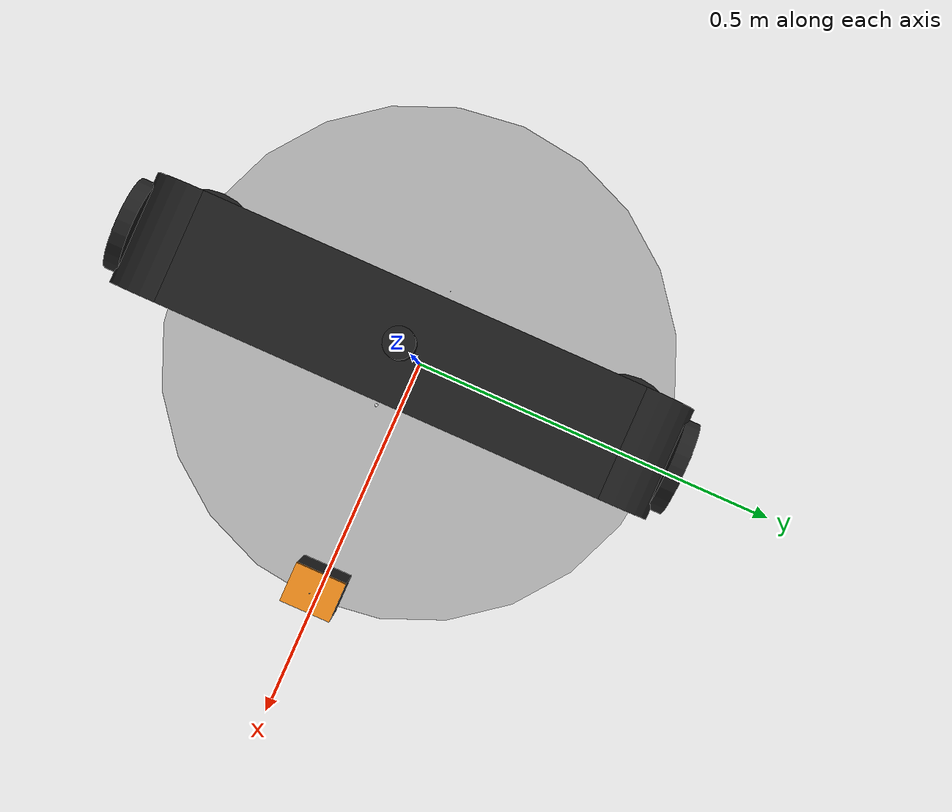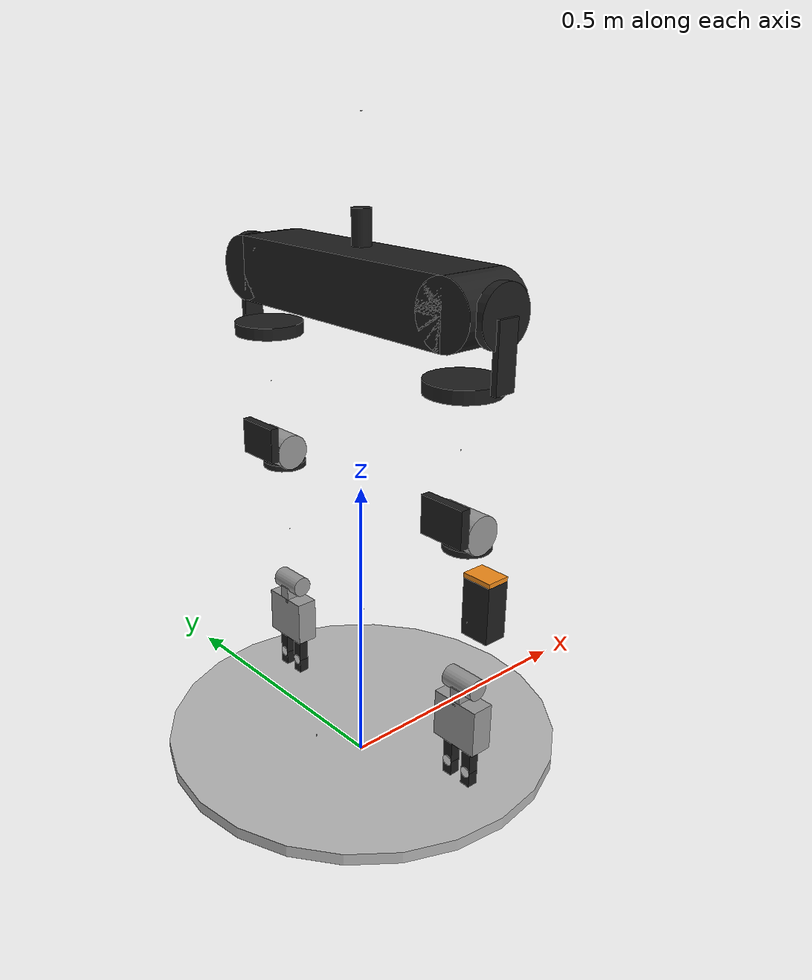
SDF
<sdf version="1.4">
  <model name="amigo">
	<!------------------------------BASE STARTS HERE---------------------------------->
	<!----------------------------CONTAINS LASER SENSOR------------------------------->
	<!-----------------------------AND A KINECT SENSOR-------------------------------->
    <link name="base_fixed_link">
      <pose>0.000000 0.000000 0.000000 0.000000 0.000000 0.000000</pose>
      <inertial>
        <pose>0.000000 0.000000 0.000000 0.000000 0.000000 0.000000</pose>
        <mass>10.000000</mass>
        <inertia>
          <ixx>0.100000</ixx>
          <ixy>0.100000</ixy>
          <ixz>0.100000</ixz>
          <iyy>0.100000</iyy>
          <iyz>0.100000</iyz>
          <izz>0.100000</izz>
        </inertia>
      </inertial>
      <velocity_decay>
        <linear>0.000000</linear>
        <angular>0.000000</angular>
      </velocity_decay>
    </link>

    <joint name="base_fixed_joint" type="revolute">
      <child>base_fixed_link</child>
      <parent>world</parent>
      <axis>
        <limit>
          <lower>0.000000</lower>
          <upper>0.000000</upper>
        </limit>
        <dynamics>
          <damping>0.000000</damping>
        </dynamics>
        <xyz>0.000000 0.000000 1.000000</xyz>
      </axis>
    </joint>

    <link name='base_x_link'>
      <pose>0.000000 0.000000 0.000000 0.000000 0.000000 0.000000</pose>
      <inertial>
        <pose>0.000000 0.000000 0.000000 0.000000 0.000000 0.000000</pose>
        <mass>10.000000</mass>
        <inertia>
          <ixx>0.100000</ixx>
          <ixy>0.100000</ixy>
          <ixz>0.100000</ixz>
          <iyy>0.100000</iyy>
          <iyz>0.100000</iyz>
          <izz>0.100000</izz>
        </inertia>
      </inertial>
      <velocity_decay>
        <linear>0.000000</linear>
        <angular>0.000000</angular>
      </velocity_decay>
    </link>

    <joint name='base_x_joint' type='prismatic'>
      <child>base_x_link</child>
      <parent>base_fixed_link</parent>
      <axis>
        <xyz>1.000000 0.000000 0.000000</xyz>
        <limit>
          <lower>-1000.000000</lower>
          <upper>1000.000000</upper>
        </limit>
        <dynamics>
          <damping>100.000000</damping>
        </dynamics>
      </axis>
    </joint>

    <link name='base_y_link'>
      <pose>0.000000 0.000000 0.000000 0.000000 0.000000 0.000000</pose>
      <inertial>
        <pose>0.000000 0.000000 0.000000 0.000000 0.000000 0.000000</pose>
        <mass>10.000000</mass>
        <inertia>
          <ixx>0.100000</ixx>
          <ixy>0.100000</ixy>
          <ixz>0.100000</ixz>
          <iyy>0.100000</iyy>
          <iyz>0.100000</iyz>
          <izz>0.100000</izz>
        </inertia>
      </inertial>
      <velocity_decay>
        <linear>0.000000</linear>
        <angular>0.000000</angular>
      </velocity_decay>
    </link>

    <joint name='base_y_joint' type='prismatic'>
      <child>base_y_link</child>
      <parent>base_x_link</parent>
      <axis>
        <xyz>0.000000 1.000000 0.000000</xyz>
        <limit>
          <lower>-1000.000000</lower>
          <upper>1000.000000</upper>
        </limit>
        <dynamics>
          <damping>100.000000</damping>
        </dynamics>
      </axis>
    </joint>

    <link name='base_link'>
      <pose>0.000000 0.000000 0.000000 0.000000 0.000000 0.000000</pose>
      <inertial>
        <pose>0.008143 0.000009 0.377224 0.000000 0.000000 0.000000</pose>
        <mass>20.643000</mass>
        <inertia>
          <ixx>3.456090</ixx>
          <ixy>-0.000056</ixy>
          <ixz>-0.040862</ixz>
          <iyy>3.508130</iyy>
          <iyz>-0.000059</iyz>
          <izz>2.464650</izz>
        </inertia>
      </inertial>

      <collision name='base_link_geom'>
        <pose>0.000000 0.000000 0.000000 0.000000 0.000000 0.000000</pose>
        <geometry>
          <cylinder>
            <length>0.000000</length>
            <radius>0.000000</radius>
          </cylinder>
        </geometry>
        <surface>
          <contact>
            <ode/>
          </contact>
          <friction>
            <ode/>
          </friction>
        </surface>
      </collision>

      <collision name='base_link_geom_base'>
        <pose>0.000000 0.000000 0.285000 0.000000 0.000000 -1.570800</pose>
        <geometry>
          <mesh>
            <scale>0.000400 0.000400 0.000400</scale>
            <uri>model://media/meshes/bottomcovers.dae</uri>
          </mesh>
        </geometry>
        <surface>
          <contact>
            <ode/>
          </contact>
          <friction>
            <ode/>
          </friction>
        </surface>
      </collision>

      <collision name='base_link_geom_base_kinect_openni_camera'>
        <pose>0.300000 0.000000 0.315000 0.000000 -0.070000 0.000000</pose>
        <geometry>
          <mesh>
            <scale>1.000000 1.000000 1.000000</scale>
            <uri>model://media/meshes/kinect_without_base.dae</uri>
          </mesh>
        </geometry>
        <surface>
          <contact>
            <ode/>
          </contact>
          <friction>
            <ode/>
          </friction>
        </surface>
      </collision>

      <collision name='base_link_geom_base_laser'>
        <pose>0.305000 0.000000 0.175000 0.000000 0.000000 0.000000</pose>
        <geometry>
          <box>
            <size>0.050000 0.065000 0.120000</size>
          </box>
        </geometry>
        <surface>
          <contact>
            <ode/>
          </contact>
          <friction>
            <ode/>
          </friction>
        </surface>
        <surface>
          <contact>
            <ode/>
          </contact>
          <friction>
            <ode/>
          </friction>
        </surface>
      </collision>

      <collision name='base_link_geom_base_plate'>
        <pose>0.000000 0.000000 0.050000 0.000000 0.000000 0.000000</pose>
        <geometry>
          <cylinder>
            <length>0.020000</length>
            <radius>0.333000</radius>
          </cylinder>
        </geometry>
        <surface>
          <contact>
            <ode/>
          </contact>
          <friction>
            <ode/>
          </friction>
        </surface>
      </collision>

      <collision name='base_link_geom_lasertop'>
        <pose>0.305000 0.000000 0.240000 0.000000 0.000000 0.000000</pose>
        <geometry>
          <box>
            <size>0.050000 0.065000 0.010000</size>
          </box>
        </geometry>
        <surface>
          <contact>
            <ode/>
          </contact>
          <friction>
            <ode/>
          </friction>
        </surface>
      </collision>

      <collision name='base_link_geom_logo'>
        <pose>0.335000 0.000000 0.100000 0.000000 0.000000 3.141500</pose>
        <geometry>
          <mesh>
            <scale>0.001600 0.001600 0.001600</scale>
            <uri>model://media/meshes/logo.dae</uri>
          </mesh>
        </geometry>
        <surface>
          <contact>
            <ode/>
          </contact>
          <friction>
            <ode/>
          </friction>
        </surface>
      </collision>

      <visual name='base_link_visual'>
        <pose>0.000000 0.000000 0.000000 0.000000 0.000000 0.000000</pose>
        <geometry>
          <cylinder>
            <length>0.000000</length>
            <radius>0.000000</radius>
          </cylinder>
        </geometry>
        <material>
          <script>
            <name>Gazebo/Red</name>
          </script>
        </material>
      </visual>

      <visual name='base_link_visualbase'>
        <pose>0.000000 0.000000 0.285000 0.000000 0.000000 -1.570800</pose>
        <geometry>
          <mesh>
            <scale>0.000400 0.000400 0.000400</scale>
            <uri>model://media/meshes/bottomcovers.dae</uri>
          </mesh>
        </geometry>
        <material>
          <script>
            <uri>model://media/materials/scripts/bottomcovers.material</uri>
			<name>amigo_robot_model_groovy/bottomcovers</name>
          </script>
        </material>
      </visual>
      <visual name='base_link_visualbase_kinect_openni_camera'>
        <pose>0.300000 0.000000 0.315000 0.000000 -0.070000 0.000000</pose>
        <geometry>
          <mesh>
            <scale>1.000000 1.000000 1.000000</scale>
            <uri>model://media/meshes/kinect_without_base.dae</uri>
          </mesh>
        </geometry>
      </visual>

      <visual name='base_link_visualbase_laser'>
        <pose>0.305000 0.000000 0.175000 0.000000 0.000000 0.000000</pose>
        <geometry>
          <box>
            <size>0.050000 0.065000 0.120000</size>
          </box>
        </geometry>
        <material>
          <script>
            <name>Gazebo/Black</name>
          </script>
        </material>
      </visual>

      <visual name='base_link_visualbase_plate'>
        <pose>0.000000 0.000000 0.050000 0.000000 0.000000 0.000000</pose>
        <geometry>
          <cylinder>
            <length>0.020000</length>
            <radius>0.333000</radius>
          </cylinder>
        </geometry>
        <material>
          <script>
            <uri>model://media/materials/scripts/aluminum.material</uri>
			<name>amigo_robot_model_groovy/aluminum</name>
          </script>
        </material>
      </visual>

      <visual name='base_link_visuallasertop'>
        <pose>0.305000 0.000000 0.240000 0.000000 0.000000 0.000000</pose>
        <geometry>
          <box>
            <size>0.050000 0.065000 0.010000</size>
          </box>
        </geometry>
        <material>
          <script>
            <uri>model://media/materials/scripts/orange.material</uri>
			<name>amigo_robot_model_groovy/orange</name>
          </script>
        </material>
      </visual>

      <visual name='base_link_visuallogo'>
        <pose>0.335000 0.000000 0.100000 0.000000 0.000000 3.141500</pose>
        <geometry>
          <mesh>
            <scale>0.001600 0.001600 0.001600</scale>
            <uri>model://media/meshes/logo.dae</uri>
          </mesh>
        </geometry>
        <material>
          <script>
            <uri>model://media/materials/scripts/logo.material</uri>
			<name>amigo_robot_model_groovy/logo</name>
          </script>
        </material>
      </visual>

      <velocity_decay>
        <linear>0.000000</linear>
        <angular>0.000000</angular>
      </velocity_decay>
      <velocity_decay>
        <linear>0.000000</linear>
        <angular>0.000000</angular>
      </velocity_decay>
      <velocity_decay>
        <linear>0.000000</linear>
        <angular>0.000000</angular>
      </velocity_decay>

      <sensor name='base_kinect_openni_camera' type='depth'>
        <update_rate>20.000000</update_rate>
        <camera name='base_kinect'>
          <horizontal_fov>1.047198</horizontal_fov>
          <image>
            <width>640</width>
            <height>480</height>
            <format>R8G8B8</format>
          </image>
          <clip>
            <near>0.050000</near>
            <far>3.000000</far>
          </clip>
        </camera>
        <plugin name='base_kinect_camera_controller' filename='libKinectPlugin.so'>
          <alwaysOn>1</alwaysOn>
          <updateRate>20</updateRate>
          <cameraName>base_kinect</cameraName>
          <imageTopicName>rgb/image_color</imageTopicName>
          <cameraInfoTopicName>rgb/camera_info</cameraInfoTopicName>
          <depthImageTopicName>depth/image</depthImageTopicName>
          <depthImageCameraInfoTopicName>depth/camera_info</depthImageCameraInfoTopicName>
          <pointCloudTopicName>rgb/points</pointCloudTopicName>
          <frameName>base_kinect/openni_depth_optical_frame</frameName>
        </plugin>
        <pose>0.300000 0.000000 0.315000 0.000000 -0.070000 0.000000</pose>
      </sensor>

      <velocity_decay>
        <linear>0.000000</linear>
        <angular>0.000000</angular>
      </velocity_decay>
      <velocity_decay>
        <linear>0.000000</linear>
        <angular>0.000000</angular>
      </velocity_decay>

      <sensor name='base_ray_sensor' type='ray'>
        <update_rate>100.000000</update_rate>
        <ray>
          <scan>
            <horizontal>
              <samples>918</samples>
              <resolution>1.000000</resolution>
              <min_angle>-2.0027654171</min_angle>
              <max_angle>1.99840199947</max_angle>
            </horizontal>
            <vertical>
              <samples>1</samples>
              <min_angle>0.000000</min_angle>
              <max_angle>0.000000</max_angle>
            </vertical>
          </scan>
          <range>
            <min>0.05</min>
            <max>60.0</max>
            <resolution>0.010000</resolution>
          </range>
        </ray>
        <plugin name='base_ros_ray_sensor_controller' filename='libLaserPlugin.so'>
          <gaussianNoise>0.005</gaussianNoise>
          <alwaysOn>1</alwaysOn>
          <updateRate>40</updateRate>
          <topicName>base_front_laser</topicName>
          <node_namespace>base</node_namespace>
          <frameName>base_laser</frameName>
        </plugin>
        <pose>0.310000 0.000000 0.240000 0.000000 0.000000 0.000000</pose>
      </sensor>

      <velocity_decay>
        <linear>0.000000</linear>
        <angular>0.000000</angular>
      </velocity_decay>
      <velocity_decay>
        <linear>0.000000</linear>
        <angular>0.000000</angular>
      </velocity_decay>
      <gravity>1</gravity>
      <velocity_decay>
        <linear>0.000000</linear>
        <angular>0.000000</angular>
      </velocity_decay>
      <self_collide>0</self_collide>
    </link>

    <joint name='base_phi_joint' type='revolute'>
      <child>base_link</child>
      <parent>base_y_link</parent>
      <axis>
        <xyz>0.000000 0.000000 1.000000</xyz>
        <limit>
          <lower>-10000000000000000.000000</lower>
          <upper>10000000000000000.000000</upper>
        </limit>
        <dynamics>
          <damping>100.000000</damping>
        </dynamics>
      </axis>
    </joint>

	<!------------------------------TORSO STARTS HERE--------------------------------->
    <link name='torso_slider'>
      <pose>0.000000 0.000000 0.635000 -0.000000 -1.570790 3.141590</pose>
      <inertial>
        <pose>0.134272 0.000000 -0.000061 0.000000 0.000000 0.000000</pose>
        <mass>16.341000</mass>
        <inertia>
          <ixx>0.090080</ixx>
          <ixy>0.000000</ixy>
          <ixz>-0.000165</ixz>
          <iyy>0.379858</iyy>
          <iyz>0.000000</iyz>
          <izz>0.389638</izz>
        </inertia>
      </inertial>

      <collision name='torso_slider_geom'>
        <pose>0.050000 0.000000 0.000000 0.000000 0.000000 1.570800</pose>
        <geometry>
          <mesh>
            <scale>0.004000 0.004000 0.004000</scale>
            <uri>model://media/meshes/torsoslidertextured.dae</uri>
          </mesh>
        </geometry>
        <surface>
          <contact>
            <ode/>
          </contact>
          <friction>
            <ode/>
          </friction>
        </surface>
      </collision>

      <collision name='torso_slider_geom_clavicles'>
        <pose>0.185000 0.000000 0.000000 0.000000 0.000000 0.000000</pose>
        <geometry>
          <box>
            <size>0.100000 0.436000 0.110000</size>
          </box>
        </geometry>
        <surface>
          <contact>
            <ode/>
          </contact>
          <friction>
            <ode/>
          </friction>
        </surface>
      </collision>

      <collision name='torso_slider_geom_shoulder_mount_left'>
        <pose>0.185000 -0.220000 0.000000 0.000000 0.000000 0.000000</pose>
        <geometry>
          <cylinder>
            <length>0.110000</length>
            <radius>0.050000</radius>
          </cylinder>
        </geometry>
        <surface>
          <contact>
            <ode/>
          </contact>
          <friction>
            <ode/>
          </friction>
        </surface>
      </collision>

      <collision name='torso_slider_geom_shoulder_mount_right'>
        <pose>0.185000 0.220000 0.000000 0.000000 0.000000 0.000000</pose>
        <geometry>
          <cylinder>
            <length>0.110000</length>
            <radius>0.050000</radius>
          </cylinder>
        </geometry>
        <surface>
          <contact>
            <ode/>
          </contact>
          <friction>
            <ode/>
          </friction>
        </surface>
      </collision>

      <collision name='torso_slider_geom_torso'>
        <pose>0.180000 0.000000 0.060000 -1.570800 -0.000000 -1.570800</pose>
        <geometry>
          <mesh>
            <scale>0.000400 0.000400 0.000400</scale>
            <uri>model://media/meshes/torsocovers.dae</uri>
          </mesh>
        </geometry>
        <surface>
          <contact>
            <ode/>
          </contact>
          <friction>
            <ode/>
          </friction>
        </surface>
      </collision>

      <collision name='torso_slider_geom_torso_assist_slider_back'>
        <pose>-0.565000 0.000000 -0.100000 1.570800 -0.000004 1.570800</pose>
        <geometry>
          <mesh>
            <scale>0.004000 0.004000 0.005000</scale>
            <uri>model://media/meshes/torsoassistslidertextured.dae</uri>
          </mesh>
        </geometry>
        <surface>
          <contact>
            <ode/>
          </contact>
          <friction>
            <ode/>
          </friction>
        </surface>
      </collision>

      <collision name='torso_slider_geom_torso_assist_slider_left'>
        <pose>-0.565000 -0.100000 0.000000 3.141590 1.570790 3.141590</pose>
        <geometry>
          <mesh>
            <scale>0.004000 0.004000 0.005000</scale>
            <uri>model://media/meshes/torsoassistslidertextured.dae</uri>
          </mesh>
        </geometry>
        <surface>
          <contact>
            <ode/>
          </contact>
          <friction>
            <ode/>
          </friction>
        </surface>
      </collision>

      <collision name='torso_slider_geom_torso_assist_slider_right'>
        <pose>-0.565000 0.100000 0.000000 3.141590 1.570790 3.141590</pose>
        <geometry>
          <mesh>
            <scale>0.004000 0.004000 0.005000</scale>
            <uri>model://media/meshes/torsoassistslidertextured.dae</uri>
          </mesh>
        </geometry>
        <surface>
          <contact>
            <ode/>
          </contact>
          <friction>
            <ode/>
          </friction>
        </surface>
      </collision>

      <visual name='torso_slider_visual'>
        <pose>0.050000 0.000000 0.000000 0.000000 0.000000 1.570800</pose>
        <geometry>
          <mesh>
            <scale>0.004000 0.004000 0.004000</scale>
            <uri>model://media/meshes/torsoslidertextured.dae</uri>
          </mesh>
        </geometry>
        <material>
          <script>
            <uri>model://media/materials/scripts/aluminum.material</uri>
			<name>amigo_robot_model_groovy/aluminum</name>
          </script>
        </material>
      </visual>

      <visual name='torso_slider_visualclavicles'>
        <pose>0.185000 0.000000 0.000000 0.000000 0.000000 0.000000</pose>
        <geometry>
          <box>
            <size>0.100000 0.436000 0.110000</size>
          </box>
        </geometry>
        <material>
          <script>
            <name>Gazebo/Black</name>
          </script>
        </material>
      </visual>

      <visual name='torso_slider_visualshoulder_mount_left'>
        <pose>0.185000 -0.220000 0.000000 0.000000 0.000000 0.000000</pose>
        <geometry>
          <cylinder>
            <length>0.110000</length>
            <radius>0.050000</radius>
          </cylinder>
        </geometry>
        <material>
          <script>
            <name>Gazebo/Black</name>
          </script>
        </material>
      </visual>

      <visual name='torso_slider_visualshoulder_mount_right'>
        <pose>0.185000 0.220000 0.000000 0.000000 0.000000 0.000000</pose>
        <geometry>
          <cylinder>
            <length>0.110000</length>
            <radius>0.050000</radius>
          </cylinder>
        </geometry>
        <material>
          <script>
            <name>Gazebo/Black</name>
          </script>
        </material>
      </visual>

      <visual name='torso_slider_visualtorso'>
        <pose>0.180000 0.000000 0.060000 -1.570800 -0.000000 -1.570800</pose>
        <geometry>
          <mesh>
            <scale>0.000400 0.000400 0.000400</scale>
            <uri>model://media/meshes/torsocovers.dae</uri>
          </mesh>
        </geometry>
        <material>
          <script>
            <uri>model://media/materials/scripts/white.material</uri>
			<name>amigo_robot_model_groovy/white</name>
          </script>
        </material>
      </visual>

      <visual name='torso_slider_visualtorso_assist_slider_back'>
        <pose>-0.565000 0.000000 -0.100000 1.570800 -0.000004 1.570800</pose>
        <geometry>
          <mesh>
            <scale>0.004000 0.004000 0.005000</scale>
            <uri>model://media/meshes/torsoassistslidertextured.dae</uri>
          </mesh>
        </geometry>
        <material>
          <script>
            <uri>model://media/materials/scripts/aluminum.material</uri>
			<name>amigo_robot_model_groovy/aluminum</name>
          </script>
        </material>
      </visual>

      <visual name='torso_slider_visualtorso_assist_slider_left'>
        <pose>-0.565000 -0.100000 0.000000 3.141590 1.570790 3.141590</pose>
        <geometry>
          <mesh>
            <scale>0.004000 0.004000 0.005000</scale>
            <uri>model://media/meshes/torsoassistslidertextured.dae</uri>
          </mesh>
        </geometry>
        <material>
          <script>
            <uri>model://media/materials/scripts/aluminum.material</uri>
			<name>amigo_robot_model_groovy/aluminum</name>
          </script>
        </material>
      </visual>

      <visual name='torso_slider_visualtorso_assist_slider_right'>
        <pose>-0.565000 0.100000 0.000000 3.141590 1.570790 3.141590</pose>
        <geometry>
          <mesh>
            <scale>0.004000 0.004000 0.005000</scale>
            <uri>model://media/meshes/torsoassistslidertextured.dae</uri>
          </mesh>
        </geometry>
        <material>
          <script>
            <uri>model://media/materials/scripts/aluminum.material</uri>
			<name>amigo_robot_model_groovy/aluminum</name>
          </script>
        </material>
      </visual>

      <velocity_decay>
        <linear>0.000000</linear>
        <angular>0.000000</angular>
      </velocity_decay>
      <velocity_decay>
        <linear>0.000000</linear>
        <angular>0.000000</angular>
      </velocity_decay>
      <velocity_decay>
        <linear>0.000000</linear>
        <angular>0.000000</angular>
      </velocity_decay>
      <velocity_decay>
        <linear>0.000000</linear>
        <angular>0.000000</angular>
      </velocity_decay>
      <velocity_decay>
        <linear>0.000000</linear>
        <angular>0.000000</angular>
      </velocity_decay>
      <velocity_decay>
        <linear>0.000000</linear>
        <angular>0.000000</angular>
      </velocity_decay>
      <velocity_decay>
        <linear>0.000000</linear>
        <angular>0.000000</angular>
      </velocity_decay>
      <gravity>1</gravity>
      <velocity_decay>
        <linear>0.000000</linear>
        <angular>0.000000</angular>
      </velocity_decay>
      <self_collide>0</self_collide>
    </link>

    <joint name='spindle_joint' type='prismatic'>
      <child>torso_slider</child>
      <parent>base_link</parent>
      <axis>
        <xyz>-0.000004 0.000000 1.000000</xyz>
        <limit>
          <lower>0.000000</lower>
          <upper>0.410000</upper>
        </limit>
        <dynamics>
          <damping>3.000000</damping>
        </dynamics>
      </axis>
    </joint>

	<!------------------------------HEAD STARTS HERE---------------------------------->
	<!---------------------------CONTAINS KINECT SENSOR------------------------------->
    <link name='neck_pan'>
      <pose>-0.000001 0.000000 0.867000 -0.001593 -0.000000 -0.000000</pose>
      <inertial>
        <pose>0.000000 0.000000 0.033500 0.000000 0.000000 0.000000</pose>
        <mass>0.050000</mass>
        <inertia>
          <ixx>0.000100</ixx>
          <ixy>0.000000</ixy>
          <ixz>0.000000</ixz>
          <iyy>0.000100</iyy>
          <iyz>0.000000</iyz>
          <izz>0.000100</izz>
        </inertia>
      </inertial>

      <collision name='neck_pan_geom'>
        <pose>0.000000 0.000000 0.033500 0.000000 0.000000 0.000000</pose>
        <geometry>
          <cylinder>
            <length>0.052500</length>
            <radius>0.015000</radius>
          </cylinder>
        </geometry>
        <surface>
          <contact>
            <ode/>
          </contact>
          <friction>
            <ode/>
          </friction>
        </surface>
      </collision>

      <visual name='neck_pan_visual'>
        <pose>0.000000 0.000000 0.033500 0.000000 0.000000 0.000000</pose>
        <geometry>
          <cylinder>
            <length>0.052500</length>
            <radius>0.015000</radius>
          </cylinder>
        </geometry>
        <material>
          <script>
            <name>Gazebo/Black</name>
          </script>
        </material>
      </visual>

      <gravity>1</gravity>
      <velocity_decay>
        <linear>0.000000</linear>
        <angular>0.000000</angular>
      </velocity_decay>
      <self_collide>0</self_collide>
    </link>

    <joint name='neck_pan_joint' type='revolute'>
      <child>neck_pan</child>
      <parent>torso_slider</parent>
      <axis>
        <xyz>0.000000 0.001593 0.999999</xyz>
        <limit>
          <lower>-1.570800</lower>
          <upper>1.570800</upper>
        </limit>
        <dynamics>
          <damping>0.100000</damping>
        </dynamics>
      </axis>
    </joint>

    <link name='neck_tilt'>
      <pose>-0.000001 0.000071 0.911500 -0.001593 -0.000000 -0.000000</pose>
      <inertial>
        <pose>0.022055 0.002575 0.041575 0.000000 0.000000 0.000000</pose>
        <mass>0.073000</mass>
        <inertia>
          <ixx>0.003416</ixx>
          <ixy>-0.000013</ixy>
          <ixz>-0.000113</ixz>
          <iyy>0.003525</iyy>
          <iyz>-0.000013</iyz>
          <izz>0.003416</izz>
        </inertia>
      </inertial>

      <collision name='neck_tilt_geom'>
        <pose>0.000000 0.000000 0.015000 0.000000 0.000000 0.000000</pose>
        <geometry>
          <mesh>
            <scale>0.004000 0.004000 0.004000</scale>
            <uri>model://media/meshes/necktilttextured.dae</uri>
          </mesh>
        </geometry>
        <surface>
          <contact>
            <ode/>
          </contact>
          <friction>
            <ode/>
          </friction>
        </surface>
      </collision>

      <collision name='neck_tilt_geom_head'>
        <pose>0.000000 0.000000 0.141000 0.000000 0.000000 -1.570800</pose>
        <geometry>
          <mesh>
            <scale>0.000400 0.000400 0.000400</scale>
            <uri>model://media/meshes/headtextured.dae</uri>
          </mesh>
        </geometry>
        <surface>
          <contact>
            <ode/>
          </contact>
          <friction>
            <ode/>
          </friction>
        </surface>
      </collision>

      <visual name='neck_tilt_visual'>
        <pose>0.000000 0.000000 0.015000 0.000000 0.000000 0.000000</pose>
        <geometry>
          <mesh>
            <scale>0.004000 0.004000 0.004000</scale>
            <uri>model://media/meshes/necktilttextured.dae</uri>
          </mesh>
        </geometry>
        <material>
          <script>
            <uri>model://media/materials/scripts/aluminum.material</uri>
			<name>amigo_robot_model_groovy/aluminum</name>
          </script>
        </material>
      </visual>

      <visual name='neck_tilt_visualhead'>
        <pose>0.000000 0.000000 0.141000 0.000000 0.000000 -1.570800</pose>
        <geometry>
          <mesh>
            <scale>0.000400 0.000400 0.000400</scale>
            <uri>model://media/meshes/headtextured.dae</uri>
          </mesh>
        </geometry>
        <material>
          <script>
            <uri>model://media/materials/scripts/white.material</uri>
			<name>amigo_robot_model_groovy/white</name>
          </script>
        </material>
      </visual>

      <visual name='neck_tilt_visualopenni_camera'>
        <pose>0.070000 0.000000 0.070000 0.000000 0.000000 0.000000</pose>
        <geometry>
          <box>
            <size>0.000000 0.000000 0.000000</size>
          </box>
        </geometry>
      </visual>

      <velocity_decay>
        <linear>0.000000</linear>
        <angular>0.000000</angular>
      </velocity_decay>
      <velocity_decay>
        <linear>0.000000</linear>
        <angular>0.000000</angular>
      </velocity_decay>
      <gravity>1</gravity>
      <velocity_decay>
        <linear>0.000000</linear>
        <angular>0.000000</angular>
      </velocity_decay>
      <self_collide>0</self_collide>

      <sensor name='openni_camera' type='depth'>
        <update_rate>20.000000</update_rate>
        <camera name='top_kinect'>
          <horizontal_fov>1.047198</horizontal_fov>
          <image>
            <width>640</width>
            <height>480</height>
            <format>R8G8B8</format>
          </image>
          <clip>
            <near>0.050000</near>
            <far>3.000000</far>
          </clip>
        </camera>
		<plugin name='kinect_camera_controller' filename='libKinectPlugin.so'>
          <alwaysOn>1</alwaysOn>
          <updateRate>20</updateRate>
          <cameraName>top_kinect</cameraName>
          <imageTopicName>rgb/image_color</imageTopicName>
          <cameraInfoTopicName>rgb/camera_info</cameraInfoTopicName>
          <depthImageTopicName>depth/image</depthImageTopicName>
          <depthImageCameraInfoTopicName>depth/camera_info</depthImageCameraInfoTopicName>
          <pointCloudTopicName>rgb/points</pointCloudTopicName>
          <frameName>top_kinect/openni_depth_optical_frame</frameName>
        </plugin>
        <pose>0.070000 0.000000 0.070000 0.000000 0.000000 0.000000</pose>
      </sensor>
    </link>

    <joint name='neck_tilt_joint' type='revolute'>
      <child>neck_tilt</child>
      <parent>neck_pan</parent>
      <axis>
        <xyz>0.000000 0.999999 -0.001593</xyz>
        <limit>
          <lower>-2.000000</lower>
          <upper>2.000000</upper>
        </limit>
        <dynamics>
          <damping>0.100000</damping>
        </dynamics>
      </axis>
    </joint>

	<!-------------------------------ARMS START HERE---------------------------------->
	<!----------------------------------LEFT ARM-------------------------------------->
    <link name='shoulder_link1_left'>
      <pose>-0.000001 0.220000 0.820000 1.570790 -0.000000 -0.000000</pose>
      <inertial>
        <pose>0.000000 0.000000 0.000000 0.000000 0.000000 0.000000</pose>
        <mass>0.100000</mass>
        <inertia>
          <ixx>0.010000</ixx>
          <ixy>0.000000</ixy>
          <ixz>0.000000</ixz>
          <iyy>0.010000</iyy>
          <iyz>0.000000</iyz>
          <izz>0.010000</izz>
        </inertia>
      </inertial>

      <collision name='shoulder_link1_left_geom'>
        <pose>0.000000 0.000000 -0.052500 0.000000 0.000000 0.000000</pose>
        <geometry>
          <cylinder>
            <length>0.015000</length>
            <radius>0.045000</radius>
          </cylinder>
        </geometry>
        <surface>
          <contact>
            <ode/>
          </contact>
          <friction>
            <ode/>
          </friction>
        </surface>
      </collision>

      <visual name='shoulder_link1_left_visual'>
        <pose>0.000000 0.000000 -0.052500 0.000000 0.000000 0.000000</pose>
        <geometry>
          <cylinder>
            <length>0.015000</length>
            <radius>0.045000</radius>
          </cylinder>
        </geometry>
        <material>
          <script>
            <name>Gazebo/Black</name>
          </script>
        </material>
      </visual>

      <gravity>1</gravity>
      <velocity_decay>
        <linear>0.000000</linear>
        <angular>0.000000</angular>
      </velocity_decay>
      <self_collide>0</self_collide>
    </link>

    <joint name='shoulder_yaw_joint_left' type='revolute'>
      <child>shoulder_link1_left</child>
      <parent>torso_slider</parent>
      <axis>
        <xyz>-1.000000 0.000000 -0.000000</xyz>
        <limit>
          <lower>-1.570000</lower>
          <upper>0.000000</upper>
        </limit>
        <dynamics>
          <damping>6.000000</damping>
        </dynamics>
      </axis>
    </joint>

    <link name='shoulder_link2_left'>
      <pose>-0.000001 0.220000 0.820000 -0.000007 -0.000000 -0.000000</pose>
      <inertial>
        <pose>0.000000 0.000000 0.000000 0.000000 0.000000 0.000000</pose>
        <mass>0.100000</mass>
        <inertia>
          <ixx>0.001000</ixx>
          <ixy>0.000000</ixy>
          <ixz>0.000000</ixz>
          <iyy>0.001000</iyy>
          <iyz>0.000000</iyz>
          <izz>0.001000</izz>
        </inertia>
      </inertial>

      <collision name='shoulder_link2_left_geom'>
        <pose>0.000000 0.060000 -0.050000 0.000000 0.000000 0.000000</pose>
        <geometry>
          <box>
            <size>0.035000 0.010000 0.100000</size>
          </box>
        </geometry>
        <surface>
          <contact>
            <ode/>
          </contact>
          <friction>
            <ode/>
          </friction>
        </surface>
      </collision>

      <visual name='shoulder_link2_left_visual'>
        <pose>0.000000 0.060000 -0.050000 0.000000 0.000000 0.000000</pose>
        <geometry>
          <box>
            <size>0.035000 0.010000 0.100000</size>
          </box>
        </geometry>
        <material>
          <script>
            <name>Gazebo/Black</name>
          </script>
        </material>
      </visual>

      <gravity>1</gravity>
      <velocity_decay>
        <linear>0.000000</linear>
        <angular>0.000000</angular>
      </velocity_decay>
      <self_collide>0</self_collide>
    </link>

    <joint name='shoulder_pitch_joint_left' type='revolute'>
      <child>shoulder_link2_left</child>
      <parent>shoulder_link1_left</parent>
      <axis>
        <xyz>-0.000000 -1.000000 0.000007</xyz>
        <limit>
          <lower>-1.570000</lower>
          <upper>1.570000</upper>
        </limit>
        <dynamics>
          <damping>6.000000</damping>
        </dynamics>
      </axis>
    </joint>

    <link name='upper_arm_left'>
      <pose>-0.000001 0.220000 0.820000 1.570790 -0.000000 -0.000000</pose>
      <inertial>
        <pose>-0.000034 -0.200410 0.000000 0.000000 0.000000 0.000000</pose>
        <mass>2.930000</mass>
        <inertia>
          <ixx>0.058022</ixx>
          <ixy>-0.000010</ixy>
          <ixz>0.000000</ixz>
          <iyy>0.033001</iyy>
          <iyz>0.000000</iyz>
          <izz>0.035023</izz>
        </inertia>
      </inertial>

      <collision name='upper_arm_left_geom'>
        <pose>-0.009590 -0.191310 -0.000010 0.000000 0.000000 3.141500</pose>
        <geometry>
          <mesh>
            <scale>0.000400 0.000400 0.000400</scale>
            <uri>model://media/meshes/upperarmtextured.dae</uri>
          </mesh>
        </geometry>
        <surface>
          <contact>
            <ode/>
          </contact>
          <friction>
            <ode/>
          </friction>
        </surface>
      </collision>

      <collision name='upper_arm_left_geom_elbow_extra_block2_left'>
        <pose>0.000000 -0.310000 0.000000 0.000000 0.000000 0.000000</pose>
        <geometry>
          <cylinder>
            <length>0.080000</length>
            <radius>0.030000</radius>
          </cylinder>
        </geometry>
        <surface>
          <contact>
            <ode/>
          </contact>
          <friction>
            <ode/>
          </friction>
        </surface>
      </collision>

      <collision name='upper_arm_left_geom_elbow_extra_block_left'>
        <pose>-0.036000 -0.290000 -0.000000 -1.570800 0.000000 0.000000</pose>
        <geometry>
          <box>
            <size>0.015000 0.080000 0.060000</size>
          </box>
        </geometry>
        <surface>
          <contact>
            <ode/>
          </contact>
          <friction>
            <ode/>
          </friction>
        </surface>
      </collision>

      <collision name='upper_arm_left_geom_upper_arm_top_left'>
        <pose>-0.010000 -0.100000 0.000000 1.570800 0.000000 0.000000</pose>
        <geometry>
          <cylinder>
            <length>0.020000</length>
            <radius>0.056100</radius>
          </cylinder>
        </geometry>
        <surface>
          <contact>
            <ode/>
          </contact>
          <friction>
            <ode/>
          </friction>
        </surface>
      </collision>

      <visual name='upper_arm_left_visual'>
        <pose>-0.009590 -0.191310 -0.000010 0.000000 0.000000 3.141500</pose>
        <geometry>
          <mesh>
            <scale>0.000400 0.000400 0.000400</scale>
            <uri>model://media/meshes/upperarmtextured.dae</uri>
          </mesh>
        </geometry>
        <material>
          <script>
            <uri>model://media/materials/scripts/white.material</uri>
			<name>amigo_robot_model_groovy/white</name>
          </script>
        </material>
      </visual>

      <visual name='upper_arm_left_visualelbow_extra_block2_left'>
        <pose>0.000000 -0.310000 0.000000 0.000000 0.000000 0.000000</pose>
        <geometry>
          <cylinder>
            <length>0.080000</length>
            <radius>0.030000</radius>
          </cylinder>
        </geometry>
        <material>
          <script>
            <name>Gazebo/Grey</name>
          </script>
        </material>
      </visual>

      <visual name='upper_arm_left_visualelbow_extra_block_left'>
        <pose>-0.036000 -0.290000 -0.000000 -1.570800 0.000000 0.000000</pose>
        <geometry>
          <box>
            <size>0.015000 0.080000 0.060000</size>
          </box>
        </geometry>
        <material>
          <script>
            <name>Gazebo/Black</name>
          </script>
        </material>
      </visual>

      <visual name='upper_arm_left_visualupper_arm_top_left'>
        <pose>-0.010000 -0.100000 0.000000 1.570800 0.000000 0.000000</pose>
        <geometry>
          <cylinder>
            <length>0.020000</length>
            <radius>0.056100</radius>
          </cylinder>
        </geometry>
        <material>
          <script>
            <name>Gazebo/Black</name>
          </script>
        </material>
      </visual>

      <velocity_decay>
        <linear>0.000000</linear>
        <angular>0.000000</angular>
      </velocity_decay>
      <velocity_decay>
        <linear>0.000000</linear>
        <angular>0.000000</angular>
      </velocity_decay>
      <velocity_decay>
        <linear>0.000000</linear>
        <angular>0.000000</angular>
      </velocity_decay>
      <gravity>1</gravity>
      <velocity_decay>
        <linear>0.000000</linear>
        <angular>0.000000</angular>
      </velocity_decay>
      <self_collide>0</self_collide>
    </link>

    <joint name='shoulder_roll_joint_left' type='revolute'>
      <child>upper_arm_left</child>
      <parent>shoulder_link2_left</parent>
      <axis>
        <xyz>-0.000000 -0.000004 -1.000000</xyz>
        <limit>
          <lower>-1.570000</lower>
          <upper>1.570000</upper>
        </limit>
        <dynamics>
          <damping>6.000000</damping>
        </dynamics>
      </axis>
    </joint>

    <link name='elbow_link4_left'>
      <pose>0.009999 0.219999 0.500000 -0.000007 -0.000000 -0.000000</pose>
      <inertial>
        <pose>0.000000 0.000000 0.000000 0.000000 0.000000 0.000000</pose>
        <mass>0.100000</mass>
        <inertia>
          <ixx>0.001000</ixx>
          <ixy>0.000000</ixy>
          <ixz>0.000000</ixz>
          <iyy>0.001000</iyy>
          <iyz>0.000000</iyz>
          <izz>0.001000</izz>
        </inertia>
      </inertial>

      <collision name='elbow_link4_left_geom'>
        <pose>0.000000 0.000000 0.000000 0.000000 0.000000 0.000000</pose>
        <geometry>
          <cylinder>
            <length>0.000000</length>
            <radius>0.000000</radius>
          </cylinder>
        </geometry>
        <surface>
          <contact>
            <ode/>
          </contact>
          <friction>
            <ode/>
          </friction>
        </surface>
      </collision>

      <visual name='elbow_link4_left_visual'>
        <pose>0.000000 0.000000 0.000000 0.000000 0.000000 0.000000</pose>
        <geometry>
          <cylinder>
            <length>0.000000</length>
            <radius>0.000000</radius>
          </cylinder>
        </geometry>
        <material>
          <script>
            <name>Gazebo/Grey</name>
          </script>
        </material>
      </visual>

      <gravity>1</gravity>
      <velocity_decay>
        <linear>0.000000</linear>
        <angular>0.000000</angular>
      </velocity_decay>
      <self_collide>0</self_collide>
    </link>

    <joint name='elbow_pitch_joint_left' type='revolute'>
      <child>elbow_link4_left</child>
      <parent>upper_arm_left</parent>
      <axis>
        <xyz>-0.000000 -1.000000 0.000007</xyz>
        <limit>
          <lower>0.000000</lower>
          <upper>2.230000</upper>
        </limit>
        <dynamics>
          <damping>2.500000</damping>
        </dynamics>
      </axis>
    </joint>

    <link name='fore_arm_left'>
      <pose>0.009999 0.219999 0.500000 1.570790 -0.000000 -0.000000</pose>
      <inertial>
        <pose>0.000182 -0.128273 0.000000 0.000000 0.000000 0.000000</pose>
        <mass>0.110000</mass>
        <inertia>
          <ixx>0.010801</ixx>
          <ixy>0.000000</ixy>
          <ixz>0.000000</ixz>
          <iyy>0.005800</iyy>
          <iyz>0.000000</iyz>
          <izz>0.005801</izz>
        </inertia>
      </inertial>

      <collision name='fore_arm_left_geom'>
        <pose>0.004250 -0.148680 0.005470 3.141590 -1.570790 3.141590</pose>
        <geometry>
          <mesh>
            <scale>0.000400 0.000400 0.000400</scale>
            <uri>model://media/meshes/forearmtextured.dae</uri>
          </mesh>
        </geometry>
        <surface>
          <contact>
            <ode/>
          </contact>
          <friction>
            <ode/>
          </friction>
        </surface>
      </collision>

      <collision name='fore_arm_left_geom_fore_arm_top_left'>
        <pose>0.002000 -0.021000 -0.000000 1.570800 0.000000 0.000000</pose>
        <geometry>
          <cylinder>
            <length>0.010000</length>
            <radius>0.037000</radius>
          </cylinder>
        </geometry>
        <surface>
          <contact>
            <ode/>
          </contact>
          <friction>
            <ode/>
          </friction>
        </surface>
      </collision>

      <visual name='fore_arm_left_visual'>
        <pose>0.004250 -0.148680 0.005470 3.141590 -1.570790 3.141590</pose>
        <geometry>
          <mesh>
            <scale>0.000400 0.000400 0.000400</scale>
            <uri>model://media/meshes/forearmtextured.dae</uri>
          </mesh>
        </geometry>
        <material>
          <script>
            <uri>model://media/materials/scripts/white.material</uri>
			<name>amigo_robot_model_groovy/white</name>
          </script>
        </material>
      </visual>

      <visual name='fore_arm_left_visualfore_arm_top_left'>
        <pose>0.002000 -0.021000 -0.000000 1.570800 0.000000 0.000000</pose>
        <geometry>
          <cylinder>
            <length>0.010000</length>
            <radius>0.037000</radius>
          </cylinder>
        </geometry>
        <material>
          <script>
            <name>Gazebo/Black</name>
          </script>
        </material>
      </visual>

      <velocity_decay>
        <linear>0.000000</linear>
        <angular>0.000000</angular>
      </velocity_decay>
      <gravity>1</gravity>
      <velocity_decay>
        <linear>0.000000</linear>
        <angular>0.000000</angular>
      </velocity_decay>
      <self_collide>0</self_collide>
    </link>

    <joint name='elbow_roll_joint_left' type='revolute'>
      <child>fore_arm_left</child>
      <parent>elbow_link4_left</parent>
      <axis>
        <xyz>-0.000000 -0.000004 -1.000000</xyz>
        <limit>
          <lower>-1.830000</lower>
          <upper>1.830000</upper>
        </limit>
        <dynamics>
          <damping>2.500000</damping>
        </dynamics>
      </axis>
    </joint>

    <link name='wrist_link6_left'>
      <pose>0.019999 0.219998 0.220000 -2.356200 1.570790 -2.356190</pose>
      <inertial>
        <pose>-0.006667 0.000000 0.000000 0.000000 0.000000 0.000000</pose>
        <mass>0.030000</mass>
        <inertia>
          <ixx>0.003000</ixx>
          <ixy>0.000000</ixy>
          <ixz>0.000000</ixz>
          <iyy>0.003004</iyy>
          <iyz>-0.000000</iyz>
          <izz>0.003004</izz>
        </inertia>
      </inertial>

      <collision name='wrist_link6_left_geom'>
        <pose>0.000000 0.000000 0.000000 1.570800 0.000000 0.000000</pose>
        <geometry>
          <cylinder>
            <length>0.000000</length>
            <radius>0.000000</radius>
          </cylinder>
        </geometry>
        <surface>
          <contact>
            <ode/>
          </contact>
          <friction>
            <ode/>
          </friction>
        </surface>
      </collision>

      <collision name='wrist_link6_left_geom_wrist_to_hand_block_left'>
        <pose>0.000000 0.000000 0.000000 0.000000 0.000000 0.000000</pose>
        <geometry>
          <box>
            <size>0.030000 0.020000 0.038000</size>
          </box>
        </geometry>
        <surface>
          <contact>
            <ode/>
          </contact>
          <friction>
            <ode/>
          </friction>
        </surface>
      </collision>

      <collision name='wrist_link6_left_geom_wrist_visual_left'>
        <pose>-0.020000 0.000000 0.000000 1.570800 0.000000 0.000000</pose>
        <geometry>
          <cylinder>
            <length>0.060000</length>
            <radius>0.018000</radius>
          </cylinder>
        </geometry>
        <surface>
          <contact>
            <ode/>
          </contact>
          <friction>
            <ode/>
          </friction>
        </surface>
      </collision>

      <visual name='wrist_link6_left_visual'>
        <pose>0.000000 0.000000 0.000000 1.570800 0.000000 0.000000</pose>
        <geometry>
          <cylinder>
            <length>0.000000</length>
            <radius>0.000000</radius>
          </cylinder>
        </geometry>
        <material>
          <script>
            <name>Gazebo/Black</name>
          </script>
        </material>
      </visual>

      <visual name='wrist_link6_left_visualwrist_to_hand_block_left'>
        <pose>0.000000 0.000000 0.000000 0.000000 0.000000 0.000000</pose>
        <geometry>
          <box>
            <size>0.030000 0.020000 0.038000</size>
          </box>
        </geometry>
        <material>
          <script>
            <name>Gazebo/Grey</name>
          </script>
        </material>
      </visual>

      <visual name='wrist_link6_left_visualwrist_visual_left'>
        <pose>-0.020000 0.000000 0.000000 1.570800 0.000000 0.000000</pose>
        <geometry>
          <cylinder>
            <length>0.060000</length>
            <radius>0.018000</radius>
          </cylinder>
        </geometry>
        <material>
          <script>
            <name>Gazebo/Grey</name>
          </script>
        </material>
      </visual>

      <velocity_decay>
        <linear>0.000000</linear>
        <angular>0.000000</angular>
      </velocity_decay>
      <velocity_decay>
        <linear>0.000000</linear>
        <angular>0.000000</angular>
      </velocity_decay>
      <gravity>1</gravity>
      <velocity_decay>
        <linear>0.000000</linear>
        <angular>0.000000</angular>
      </velocity_decay>
      <self_collide>0</self_collide>
    </link>

    <joint name='wrist_pitch_joint_left' type='revolute'>
      <child>wrist_link6_left</child>
      <parent>fore_arm_left</parent>
      <axis>
        <xyz>0.000004 -1.000000 0.000004</xyz>
        <limit>
          <lower>-0.950000</lower>
          <upper>0.950000</upper>
        </limit>
        <dynamics>
          <damping>0.500000</damping>
        </dynamics>
      </axis>
    </joint>

    <link name='hand_left'>
      <pose>0.019999 0.219998 0.220000 -2.356200 1.570790 -2.356190</pose>
      <inertial>
        <pose>0.047623 0.000000 0.000000 0.000000 0.000000 0.000000</pose>
        <mass>0.210010</mass>
        <inertia>
          <ixx>0.011100</ixx>
          <ixy>0.000000</ixy>
          <ixz>0.000000</ixz>
          <iyy>0.011016</iyy>
          <iyz>0.000000</iyz>
          <izz>0.011016</izz>
        </inertia>
      </inertial>

      <collision name='hand_left_geom'>
        <pose>0.048000 0.000000 0.000000 0.000000 0.000000 0.000000</pose>
        <geometry>
          <box>
            <size>0.080000 0.085000 0.038000</size>
          </box>
        </geometry>
        <surface>
          <contact>
            <ode/>
          </contact>
          <friction>
            <ode/>
          </friction>
        </surface>
      </collision>

      <collision name='hand_left_geom_grippoint_left'>
        <pose>0.040000 0.000000 0.000000 0.000000 0.000000 0.000000</pose>
        <geometry>
          <box>
            <size>0.000000 0.000000 0.000000</size>
          </box>
        </geometry>
        <surface>
          <contact>
            <ode/>
          </contact>
          <friction>
            <ode/>
          </friction>
        </surface>
      </collision>

      <collision name='hand_left_geom_hand_marker_left'>
        <pose>0.140000 0.000000 0.000000 0.000000 0.000000 0.000000</pose>
        <geometry>
          <cylinder>
            <length>0.000000</length>
            <radius>0.000000</radius>
          </cylinder>
        </geometry>
        <surface>
          <contact>
            <ode/>
          </contact>
          <friction>
            <ode/>
          </friction>
        </surface>
      </collision>

      <visual name='hand_left_visual'>
        <pose>0.048000 0.000000 0.000000 0.000000 0.000000 0.000000</pose>
        <geometry>
          <box>
            <size>0.080000 0.085000 0.038000</size>
          </box>
        </geometry>
        <material>
          <script>
            <name>Gazebo/Grey</name>
          </script>
        </material>
      </visual>

      <visual name='hand_left_visualgrippoint_left'>
        <pose>0.040000 0.000000 0.000000 0.000000 0.000000 0.000000</pose>
        <geometry>
          <box>
            <size>0.000000 0.000000 0.000000</size>
          </box>
        </geometry>
        <material>
          <script>
            <name>Gazebo/Blue</name>
          </script>
        </material>
      </visual>

      <visual name='hand_left_visualhand_marker_left'>
        <pose>0.140000 0.000000 0.000000 0.000000 0.000000 0.000000</pose>
        <geometry>
          <cylinder>
            <length>0.000000</length>
            <radius>0.000000</radius>
          </cylinder>
        </geometry>
        <material>
          <script>
            <name>Gazebo/Grey</name>
          </script>
        </material>
      </visual>

      <velocity_decay>
        <linear>0.000000</linear>
        <angular>0.000000</angular>
      </velocity_decay>
      <velocity_decay>
        <linear>0.000000</linear>
        <angular>0.000000</angular>
      </velocity_decay>
      <gravity>1</gravity>
      <velocity_decay>
        <linear>0.000000</linear>
        <angular>0.000000</angular>
      </velocity_decay>
      <self_collide>0</self_collide>
    </link>

    <joint name='wrist_yaw_joint_left' type='revolute'>
      <child>hand_left</child>
      <parent>wrist_link6_left</parent>
      <axis>
        <xyz>-1.010000 -0.000004 0.000004</xyz>
        <limit>
          <lower>-0.610000</lower>
          <upper>0.610000</upper>
        </limit>
        <dynamics>
          <damping>0.500000</damping>
        </dynamics>
      </axis>
    </joint>

    <link name='finger1_left'>
      <pose>0.019999 0.239998 0.145000 -0.000004 0.000800 0.000004</pose>
      <inertial>
        <pose>0.000000 0.000000 -0.035000 0.000000 0.000000 0.000000</pose>
        <mass>0.060000</mass>
        <inertia>
          <ixx>0.011036</ixx>
          <ixy>0.000000</ixy>
          <ixz>-0.000000</ixz>
          <iyy>0.011036</iyy>
          <iyz>0.000000</iyz>
          <izz>0.011000</izz>
        </inertia>
      </inertial>

      <collision name='finger1_left_geom'>
        <pose>0.000000 0.000000 -0.030000 0.000000 0.000000 0.000000</pose>
        <geometry>
          <box>
            <size>0.018000 0.018000 0.060000</size>
          </box>
        </geometry>
        <surface>
          <contact>
            <ode/>
          </contact>
          <friction>
            <ode/>
          </friction>
        </surface>
        <surface>
          <contact>
            <ode/>
          </contact>
          <friction>
            <ode>
              <mu>100.000000</mu>
              <mu2>100.000000</mu2>
            </ode>
          </friction>
        </surface>
      </collision>

      <collision name='finger1_left_geom_finger1_phalanx_left'>
        <pose>0.000000 0.000000 -0.060000 0.000000 1.570000 0.000000</pose>
        <geometry>
          <cylinder>
            <length>0.019000</length>
            <radius>0.009000</radius>
          </cylinder>
        </geometry>
        <surface>
          <contact>
            <ode/>
          </contact>
          <friction>
            <ode/>
          </friction>
        </surface>
      </collision>

      <visual name='finger1_left_visual'>
        <pose>0.000000 0.000000 -0.030000 0.000000 0.000000 0.000000</pose>
        <geometry>
          <box>
            <size>0.018000 0.018000 0.060000</size>
          </box>
        </geometry>
        <material>
          <script>
            <name>Gazebo/Black</name>
          </script>
        </material>
      </visual>

      <visual name='finger1_left_visualfinger1_phalanx_left'>
        <pose>0.000000 0.000000 -0.060000 0.000000 1.570000 0.000000</pose>
        <geometry>
          <cylinder>
            <length>0.019000</length>
            <radius>0.009000</radius>
          </cylinder>
        </geometry>
        <material>
          <script>
            <name>Gazebo/White</name>
          </script>
        </material>
      </visual>

      <velocity_decay>
        <linear>0.000000</linear>
        <angular>0.000000</angular>
      </velocity_decay>
      <velocity_decay>
        <linear>0.000000</linear>
        <angular>0.000000</angular>
      </velocity_decay>
      <gravity>1</gravity>
      <velocity_decay>
        <linear>0.000000</linear>
        <angular>0.000000</angular>
      </velocity_decay>
      <self_collide>0</self_collide>
    </link>

    <joint name='finger1_joint_left' type='revolute'>
      <child>finger1_left</child>
      <parent>hand_left</parent>
      <axis>
        <xyz>1.000000 0.000004 -0.000800</xyz>
        <limit>
          <lower>-1.570000</lower>
          <upper>1.570000</upper>
        </limit>
        <dynamics>
          <damping>0.500000</damping>
        </dynamics>
      </axis>
    </joint>

    <link name='finger1_tip_left'>
      <pose>0.019951 0.239997 0.085000 -0.000004 0.000800 0.000004</pose>
      <inertial>
        <pose>0.000000 0.000000 -0.035000 0.000000 0.000000 0.000000</pose>
        <mass>0.060000</mass>
        <inertia>
          <ixx>0.001406</ixx>
          <ixy>0.000000</ixy>
          <ixz>-0.000000</ixz>
          <iyy>0.001556</iyy>
          <iyz>0.000000</iyz>
          <izz>0.001520</izz>
        </inertia>
      </inertial>

      <collision name='finger1_tip_left_geom'>
        <pose>0.000000 0.000000 -0.030000 0.000000 0.000000 0.000000</pose>
        <geometry>
          <box>
            <size>0.018000 0.018000 0.060000</size>
          </box>
        </geometry>
        <surface>
          <contact>
            <ode/>
          </contact>
          <friction>
            <ode/>
          </friction>
        </surface>
        <surface>
          <contact>
            <ode/>
          </contact>
          <friction>
            <ode>
              <mu>100.000000</mu>
              <mu2>100.000000</mu2>
            </ode>
          </friction>
        </surface>
      </collision>

      <collision name='finger1_tip_left_geom_finger1_tip_phalanx_left'>
        <pose>0.000000 0.000000 -0.060000 0.000000 1.570000 0.000000</pose>
        <geometry>
          <cylinder>
            <length>0.017000</length>
            <radius>0.009000</radius>
          </cylinder>
        </geometry>
        <surface>
          <contact>
            <ode/>
          </contact>
          <friction>
            <ode/>
          </friction>
        </surface>
      </collision>

      <visual name='finger1_tip_left_visual'>
        <pose>0.000000 0.000000 -0.030000 0.000000 0.000000 0.000000</pose>
        <geometry>
          <box>
            <size>0.018000 0.018000 0.060000</size>
          </box>
        </geometry>
        <material>
          <script>
            <name>Gazebo/Black</name>
          </script>
        </material>
      </visual>

      <visual name='finger1_tip_left_visualfinger1_tip_phalanx_left'>
        <pose>0.000000 0.000000 -0.060000 0.000000 1.570000 0.000000</pose>
        <geometry>
          <cylinder>
            <length>0.017000</length>
            <radius>0.009000</radius>
          </cylinder>
        </geometry>
        <material>
          <script>
            <name>Gazebo/White</name>
          </script>
        </material>
      </visual>

      <velocity_decay>
        <linear>0.000000</linear>
        <angular>0.000000</angular>
      </velocity_decay>
      <velocity_decay>
        <linear>0.000000</linear>
        <angular>0.000000</angular>
      </velocity_decay>
      <gravity>1</gravity>
      <velocity_decay>
        <linear>0.000000</linear>
        <angular>0.000000</angular>
      </velocity_decay>
      <self_collide>0</self_collide>
    </link>

    <joint name='finger1_tip_joint_left' type='revolute'>
      <child>finger1_tip_left</child>
      <parent>finger1_left</parent>
      <axis>
        <xyz>1.000000 0.000004 -0.000800</xyz>
        <limit>
          <lower>-1.570000</lower>
          <upper>1.570000</upper>
        </limit>
        <dynamics>
          <damping>0.500000</damping>
        </dynamics>
      </axis>
    </joint>

    <link name='finger2_left'>
      <pose>0.019999 0.199998 0.145000 -0.000004 0.000800 0.000004</pose>
      <inertial>
        <pose>0.000000 0.000000 -0.035000 0.000000 0.000000 0.000000</pose>
        <mass>0.060000</mass>
        <inertia>
          <ixx>0.011036</ixx>
          <ixy>0.000000</ixy>
          <ixz>-0.000000</ixz>
          <iyy>0.011036</iyy>
          <iyz>0.000000</iyz>
          <izz>0.011000</izz>
        </inertia>
      </inertial>

      <collision name='finger2_left_geom'>
        <pose>0.000000 0.000000 -0.030000 0.000000 0.000000 0.000000</pose>
        <geometry>
          <box>
            <size>0.018000 0.018000 0.060000</size>
          </box>
        </geometry>
        <surface>
          <contact>
            <ode/>
          </contact>
          <friction>
            <ode/>
          </friction>
        </surface>
        <surface>
          <contact>
            <ode/>
          </contact>
          <friction>
            <ode>
              <mu>100.000000</mu>
              <mu2>100.000000</mu2>
            </ode>
          </friction>
        </surface>
      </collision>

      <collision name='finger2_left_geom_finger2_phalanx_left'>
        <pose>0.000000 0.000000 -0.060000 0.000000 1.570000 0.000000</pose>
        <geometry>
          <cylinder>
            <length>0.019000</length>
            <radius>0.009000</radius>
          </cylinder>
        </geometry>
        <surface>
          <contact>
            <ode/>
          </contact>
          <friction>
            <ode/>
          </friction>
        </surface>
      </collision>

      <visual name='finger2_left_visual'>
        <pose>0.000000 0.000000 -0.030000 0.000000 0.000000 0.000000</pose>
        <geometry>
          <box>
            <size>0.018000 0.018000 0.060000</size>
          </box>
        </geometry>
        <material>
          <script>
            <name>Gazebo/Black</name>
          </script>
        </material>
      </visual>

      <visual name='finger2_left_visualfinger2_phalanx_left'>
        <pose>0.000000 0.000000 -0.060000 0.000000 1.570000 0.000000</pose>
        <geometry>
          <cylinder>
            <length>0.019000</length>
            <radius>0.009000</radius>
          </cylinder>
        </geometry>
        <material>
          <script>
            <name>Gazebo/White</name>
          </script>
        </material>
      </visual>

      <velocity_decay>
        <linear>0.000000</linear>
        <angular>0.000000</angular>
      </velocity_decay>
      <velocity_decay>
        <linear>0.000000</linear>
        <angular>0.000000</angular>
      </velocity_decay>
      <gravity>1</gravity>
      <velocity_decay>
        <linear>0.000000</linear>
        <angular>0.000000</angular>
      </velocity_decay>
      <self_collide>0</self_collide>
    </link>

    <joint name='finger2_joint_left' type='revolute'>
      <child>finger2_left</child>
      <parent>hand_left</parent>
      <axis>
        <xyz>-1.000000 -0.000004 0.000800</xyz>
        <limit>
          <lower>-1.570000</lower>
          <upper>1.570000</upper>
        </limit>
        <dynamics>
          <damping>0.500000</damping>
        </dynamics>
      </axis>
    </joint>

    <link name='finger2_tip_left'>
      <pose>0.019951 0.199997 0.085000 -0.000004 0.000800 0.000004</pose>
      <inertial>
        <pose>0.000000 0.000000 -0.035000 0.000000 0.000000 0.000000</pose>
        <mass>0.060000</mass>
        <inertia>
          <ixx>0.001406</ixx>
          <ixy>0.000000</ixy>
          <ixz>-0.000000</ixz>
          <iyy>0.001556</iyy>
          <iyz>0.000000</iyz>
          <izz>0.001520</izz>
        </inertia>
      </inertial>

      <collision name='finger2_tip_left_geom'>
        <pose>0.000000 0.000000 -0.030000 0.000000 0.000000 0.000000</pose>
        <geometry>
          <box>
            <size>0.018000 0.018000 0.060000</size>
          </box>
        </geometry>
        <surface>
          <contact>
            <ode/>
          </contact>
          <friction>
            <ode/>
          </friction>
        </surface>
        <surface>
          <contact>
            <ode/>
          </contact>
          <friction>
            <ode>
              <mu>100.000000</mu>
              <mu2>100.000000</mu2>
            </ode>
          </friction>
        </surface>
      </collision>

      <collision name='finger2_tip_left_geom_finger2_tip_phalanx_left'>
        <pose>0.000000 0.000000 -0.060000 0.000000 1.570000 0.000000</pose>
        <geometry>
          <cylinder>
            <length>0.017000</length>
            <radius>0.009000</radius>
          </cylinder>
        </geometry>
        <surface>
          <contact>
            <ode/>
          </contact>
          <friction>
            <ode/>
          </friction>
        </surface>
      </collision>

      <visual name='finger2_tip_left_visual'>
        <pose>0.000000 0.000000 -0.030000 0.000000 0.000000 0.000000</pose>
        <geometry>
          <box>
            <size>0.018000 0.018000 0.060000</size>
          </box>
        </geometry>
        <material>
          <script>
            <name>Gazebo/Black</name>
          </script>
        </material>
      </visual>

      <visual name='finger2_tip_left_visualfinger2_tip_phalanx_left'>
        <pose>0.000000 0.000000 -0.060000 0.000000 1.570000 0.000000</pose>
        <geometry>
          <cylinder>
            <length>0.017000</length>
            <radius>0.009000</radius>
          </cylinder>
        </geometry>
        <material>
          <script>
            <name>Gazebo/White</name>
          </script>
        </material>
      </visual>

      <velocity_decay>
        <linear>0.000000</linear>
        <angular>0.000000</angular>
      </velocity_decay>
      <velocity_decay>
        <linear>0.000000</linear>
        <angular>0.000000</angular>
      </velocity_decay>
      <gravity>1</gravity>
      <velocity_decay>
        <linear>0.000000</linear>
        <angular>0.000000</angular>
      </velocity_decay>
      <self_collide>0</self_collide>
    </link>

    <joint name='finger2_tip_joint_left' type='revolute'>
      <child>finger2_tip_left</child>
      <parent>finger2_left</parent>
      <axis>
        <xyz>-1.000000 -0.000004 0.000800</xyz>
        <limit>
          <lower>-1.570000</lower>
          <upper>1.570000</upper>
        </limit>
        <dynamics>
          <damping>0.500000</damping>
        </dynamics>
      </axis>
    </joint>

	<!----------------------------------RIGHT ARM-------------------------------------->
    <link name='shoulder_link1_right'>
      <pose>-0.000001 -0.220000 0.820000 1.570790 -0.000000 -0.000000</pose>
      <inertial>
        <pose>0.000000 0.000000 0.000000 0.000000 0.000000 0.000000</pose>
        <mass>0.100000</mass>
        <inertia>
          <ixx>0.010000</ixx>
          <ixy>0.000000</ixy>
          <ixz>0.000000</ixz>
          <iyy>0.010000</iyy>
          <iyz>0.000000</iyz>
          <izz>0.010000</izz>
        </inertia>
      </inertial>

      <collision name='shoulder_link1_right_geom'>
        <pose>0.000000 0.000000 0.052500 0.000000 0.000000 0.000000</pose>
        <geometry>
          <cylinder>
            <length>0.015000</length>
            <radius>0.045000</radius>
          </cylinder>
        </geometry>
        <surface>
          <contact>
            <ode/>
          </contact>
          <friction>
            <ode/>
          </friction>
        </surface>
      </collision>

      <visual name='shoulder_link1_right_visual'>
        <pose>0.000000 0.000000 0.052500 0.000000 0.000000 0.000000</pose>
        <geometry>
          <cylinder>
            <length>0.015000</length>
            <radius>0.045000</radius>
          </cylinder>
        </geometry>
        <material>
          <script>
            <name>Gazebo/Black</name>
          </script>
        </material>
      </visual>

      <gravity>1</gravity>
      <velocity_decay>
        <linear>0.000000</linear>
        <angular>0.000000</angular>
      </velocity_decay>
      <self_collide>0</self_collide>
    </link>

    <joint name='shoulder_yaw_joint_right' type='revolute'>
      <child>shoulder_link1_right</child>
      <parent>torso_slider</parent>
      <axis>
        <xyz>1.000000 -0.000000 0.000000</xyz>
        <limit>
          <lower>-1.570000</lower>
          <upper>0.000000</upper>
        </limit>
        <dynamics>
          <damping>6.000000</damping>
        </dynamics>
      </axis>
    </joint>

    <link name='shoulder_link2_right'>
      <pose>-0.000001 -0.220000 0.820000 -0.000007 -0.000000 -0.000000</pose>
      <inertial>
        <pose>0.000000 0.000000 0.000000 0.000000 0.000000 0.000000</pose>
        <mass>0.100000</mass>
        <inertia>
          <ixx>0.001000</ixx>
          <ixy>0.000000</ixy>
          <ixz>0.000000</ixz>
          <iyy>0.001000</iyy>
          <iyz>0.000000</iyz>
          <izz>0.001000</izz>
        </inertia>
      </inertial>

      <collision name='shoulder_link2_right_geom'>
        <pose>0.000000 -0.060000 -0.050000 0.000000 0.000000 0.000000</pose>
        <geometry>
          <box>
            <size>0.035000 0.010000 0.100000</size>
          </box>
        </geometry>
        <surface>
          <contact>
            <ode/>
          </contact>
          <friction>
            <ode/>
          </friction>
        </surface>
      </collision>

      <visual name='shoulder_link2_right_visual'>
        <pose>0.000000 -0.060000 -0.050000 0.000000 0.000000 0.000000</pose>
        <geometry>
          <box>
            <size>0.035000 0.010000 0.100000</size>
          </box>
        </geometry>
        <material>
          <script>
            <name>Gazebo/Black</name>
          </script>
        </material>
      </visual>

      <gravity>1</gravity>
      <velocity_decay>
        <linear>0.000000</linear>
        <angular>0.000000</angular>
      </velocity_decay>
      <self_collide>0</self_collide>
    </link>

    <joint name='shoulder_pitch_joint_right' type='revolute'>
      <child>shoulder_link2_right</child>
      <parent>shoulder_link1_right</parent>
      <axis>
        <xyz>-0.000000 -1.000000 0.000007</xyz>
        <limit>
          <lower>-1.570000</lower>
          <upper>1.570000</upper>
        </limit>
        <dynamics>
          <damping>6.000000</damping>
        </dynamics>
      </axis>
    </joint>

    <link name='upper_arm_right'>
      <pose>-0.000001 -0.220000 0.820000 1.570790 -0.000000 -0.000000</pose>
      <inertial>
        <pose>-0.000034 -0.200410 0.000000 0.000000 0.000000 0.000000</pose>
        <mass>2.930000</mass>
        <inertia>
          <ixx>0.058022</ixx>
          <ixy>-0.000010</ixy>
          <ixz>0.000000</ixz>
          <iyy>0.033001</iyy>
          <iyz>0.000000</iyz>
          <izz>0.035023</izz>
        </inertia>
      </inertial>

      <collision name='upper_arm_right_geom'>
        <pose>-0.009590 -0.191310 -0.000010 0.000000 0.000000 3.141500</pose>
        <geometry>
          <mesh>
            <scale>0.000400 0.000400 0.000400</scale>
            <uri>model://media/meshes/upperarmtextured.dae</uri>
          </mesh>
        </geometry>
        <surface>
          <contact>
            <ode/>
          </contact>
          <friction>
            <ode/>
          </friction>
        </surface>
      </collision>

      <collision name='upper_arm_right_geom_elbow_extra_block2_right'>
        <pose>0.000000 -0.310000 0.000000 0.000000 0.000000 0.000000</pose>
        <geometry>
          <cylinder>
            <length>0.080000</length>
            <radius>0.030000</radius>
          </cylinder>
        </geometry>
        <surface>
          <contact>
            <ode/>
          </contact>
          <friction>
            <ode/>
          </friction>
        </surface>
      </collision>

      <collision name='upper_arm_right_geom_elbow_extra_block_right'>
        <pose>-0.036000 -0.290000 -0.000000 -1.570800 0.000000 0.000000</pose>
        <geometry>
          <box>
            <size>0.015000 0.080000 0.060000</size>
          </box>
        </geometry>
        <surface>
          <contact>
            <ode/>
          </contact>
          <friction>
            <ode/>
          </friction>
        </surface>
      </collision>

      <collision name='upper_arm_right_geom_upper_arm_top_right'>
        <pose>-0.010000 -0.100000 0.000000 1.570800 0.000000 0.000000</pose>
        <geometry>
          <cylinder>
            <length>0.020000</length>
            <radius>0.056100</radius>
          </cylinder>
        </geometry>
        <surface>
          <contact>
            <ode/>
          </contact>
          <friction>
            <ode/>
          </friction>
        </surface>
      </collision>

      <visual name='upper_arm_right_visual'>
        <pose>-0.009590 -0.191310 -0.000010 0.000000 0.000000 3.141500</pose>
        <geometry>
          <mesh>
            <scale>0.000400 0.000400 0.000400</scale>
            <uri>model://media/meshes/upperarmtextured.dae</uri>
          </mesh>
        </geometry>
        <material>
          <script>
            <uri>model://media/materials/scripts/white.material</uri>
			<name>amigo_robot_model_groovy/white</name>
          </script>
        </material>
      </visual>

      <visual name='upper_arm_right_visualelbow_extra_block2_right'>
        <pose>0.000000 -0.310000 0.000000 0.000000 0.000000 0.000000</pose>
        <geometry>
          <cylinder>
            <length>0.080000</length>
            <radius>0.030000</radius>
          </cylinder>
        </geometry>
        <material>
          <script>
            <name>Gazebo/Grey</name>
          </script>
        </material>
      </visual>

      <visual name='upper_arm_right_visualelbow_extra_block_right'>
        <pose>-0.036000 -0.290000 -0.000000 -1.570800 0.000000 0.000000</pose>
        <geometry>
          <box>
            <size>0.015000 0.080000 0.060000</size>
          </box>
        </geometry>
        <material>
          <script>
            <name>Gazebo/Black</name>
          </script>
        </material>
      </visual>

      <visual name='upper_arm_right_visualupper_arm_top_right'>
        <pose>-0.010000 -0.100000 0.000000 1.570800 0.000000 0.000000</pose>
        <geometry>
          <cylinder>
            <length>0.020000</length>
            <radius>0.056100</radius>
          </cylinder>
        </geometry>
        <material>
          <script>
            <name>Gazebo/Black</name>
          </script>
        </material>
      </visual>

      <velocity_decay>
        <linear>0.000000</linear>
        <angular>0.000000</angular>
      </velocity_decay>
      <velocity_decay>
        <linear>0.000000</linear>
        <angular>0.000000</angular>
      </velocity_decay>
      <velocity_decay>
        <linear>0.000000</linear>
        <angular>0.000000</angular>
      </velocity_decay>
      <gravity>1</gravity>
      <velocity_decay>
        <linear>0.000000</linear>
        <angular>0.000000</angular>
      </velocity_decay>
      <self_collide>0</self_collide>
    </link>

    <joint name='shoulder_roll_joint_right' type='revolute'>
      <child>upper_arm_right</child>
      <parent>shoulder_link2_right</parent>
      <axis>
        <xyz>0.000000 0.000004 1.000000</xyz>
        <limit>
          <lower>-1.570000</lower>
          <upper>1.570000</upper>
        </limit>
        <dynamics>
          <damping>6.000000</damping>
        </dynamics>
      </axis>
    </joint>

    <link name='elbow_link4_right'>
      <pose>0.009999 -0.220001 0.500000 -0.000007 -0.000000 -0.000000</pose>
      <inertial>
        <pose>0.000000 0.000000 0.000000 0.000000 0.000000 0.000000</pose>
        <mass>0.100000</mass>
        <inertia>
          <ixx>0.001000</ixx>
          <ixy>0.000000</ixy>
          <ixz>0.000000</ixz>
          <iyy>0.001000</iyy>
          <iyz>0.000000</iyz>
          <izz>0.001000</izz>
        </inertia>
      </inertial>

      <collision name='elbow_link4_right_geom'>
        <pose>0.000000 0.000000 0.000000 0.000000 0.000000 0.000000</pose>
        <geometry>
          <cylinder>
            <length>0.000000</length>
            <radius>0.000000</radius>
          </cylinder>
        </geometry>
        <surface>
          <contact>
            <ode/>
          </contact>
          <friction>
            <ode/>
          </friction>
        </surface>
      </collision>

      <visual name='elbow_link4_right_visual'>
        <pose>0.000000 0.000000 0.000000 0.000000 0.000000 0.000000</pose>
        <geometry>
          <cylinder>
            <length>0.000000</length>
            <radius>0.000000</radius>
          </cylinder>
        </geometry>
        <material>
          <script>
            <name>Gazebo/Grey</name>
          </script>
        </material>
      </visual>

      <gravity>1</gravity>
      <velocity_decay>
        <linear>0.000000</linear>
        <angular>0.000000</angular>
      </velocity_decay>
      <self_collide>0</self_collide>
    </link>

    <joint name='elbow_pitch_joint_right' type='revolute'>
      <child>elbow_link4_right</child>
      <parent>upper_arm_right</parent>
      <axis>
        <xyz>-0.000000 -1.000000 0.000007</xyz>
        <limit>
          <lower>0.000000</lower>
          <upper>2.230000</upper>
        </limit>
        <dynamics>
          <damping>2.500000</damping>
        </dynamics>
      </axis>
    </joint>

    <link name='fore_arm_right'>
      <pose>0.009999 -0.220001 0.500000 1.570790 -0.000000 -0.000000</pose>
      <inertial>
        <pose>0.000182 -0.128273 0.000000 0.000000 0.000000 0.000000</pose>
        <mass>0.110000</mass>
        <inertia>
          <ixx>0.010801</ixx>
          <ixy>0.000000</ixy>
          <ixz>0.000000</ixz>
          <iyy>0.005800</iyy>
          <iyz>0.000000</iyz>
          <izz>0.005801</izz>
        </inertia>
      </inertial>

      <collision name='fore_arm_right_geom'>
        <pose>0.004250 -0.148680 0.005470 3.141590 -1.570790 3.141590</pose>
        <geometry>
          <mesh>
            <scale>0.000400 0.000400 0.000400</scale>
            <uri>model://media/meshes/forearmtextured.dae</uri>
          </mesh>
        </geometry>
        <surface>
          <contact>
            <ode/>
          </contact>
          <friction>
            <ode/>
          </friction>
        </surface>
      </collision>

      <collision name='fore_arm_right_geom_fore_arm_top_right'>
        <pose>0.002000 -0.021000 -0.000000 1.570800 0.000000 0.000000</pose>
        <geometry>
          <cylinder>
            <length>0.010000</length>
            <radius>0.037000</radius>
          </cylinder>
        </geometry>
        <surface>
          <contact>
            <ode/>
          </contact>
          <friction>
            <ode/>
          </friction>
        </surface>
      </collision>

      <visual name='fore_arm_right_visual'>
        <pose>0.004250 -0.148680 0.005470 3.141590 -1.570790 3.141590</pose>
        <geometry>
          <mesh>
            <scale>0.000400 0.000400 0.000400</scale>
            <uri>model://media/meshes/forearmtextured.dae</uri>
          </mesh>
        </geometry>
        <material>
          <script>
            <uri>model://media/materials/scripts/white.material</uri>
			<name>amigo_robot_model_groovy/white</name>
          </script>
        </material>
      </visual>

      <visual name='fore_arm_right_visualfore_arm_top_right'>
        <pose>0.002000 -0.021000 -0.000000 1.570800 0.000000 0.000000</pose>
        <geometry>
          <cylinder>
            <length>0.010000</length>
            <radius>0.037000</radius>
          </cylinder>
        </geometry>
        <material>
          <script>
            <name>Gazebo/Black</name>
          </script>
        </material>
      </visual>

      <velocity_decay>
        <linear>0.000000</linear>
        <angular>0.000000</angular>
      </velocity_decay>
      <gravity>1</gravity>
      <velocity_decay>
        <linear>0.000000</linear>
        <angular>0.000000</angular>
      </velocity_decay>
      <self_collide>0</self_collide>
    </link>

    <joint name='elbow_roll_joint_right' type='revolute'>
      <child>fore_arm_right</child>
      <parent>elbow_link4_right</parent>
      <axis>
        <xyz>0.000000 0.000004 1.000000</xyz>
        <limit>
          <lower>-1.830000</lower>
          <upper>1.830000</upper>
        </limit>
        <dynamics>
          <damping>2.500000</damping>
        </dynamics>
      </axis>
    </joint>

    <link name='wrist_link6_right'>
      <pose>0.019999 -0.220002 0.220000 -2.356200 1.570790 -2.356190</pose>
      <inertial>
        <pose>-0.006667 0.000000 0.000000 0.000000 0.000000 0.000000</pose>
        <mass>0.030000</mass>
        <inertia>
          <ixx>0.003000</ixx>
          <ixy>0.000000</ixy>
          <ixz>0.000000</ixz>
          <iyy>0.003004</iyy>
          <iyz>-0.000000</iyz>
          <izz>0.003004</izz>
        </inertia>
      </inertial>

      <collision name='wrist_link6_right_geom'>
        <pose>0.000000 0.000000 0.000000 1.570800 0.000000 0.000000</pose>
        <geometry>
          <cylinder>
            <length>0.000000</length>
            <radius>0.000000</radius>
          </cylinder>
        </geometry>
        <surface>
          <contact>
            <ode/>
          </contact>
          <friction>
            <ode/>
          </friction>
        </surface>
      </collision>

      <collision name='wrist_link6_right_geom_wrist_to_hand_block_right'>
        <pose>0.000000 0.000000 0.000000 0.000000 0.000000 0.000000</pose>
        <geometry>
          <box>
            <size>0.030000 0.020000 0.038000</size>
          </box>
        </geometry>
        <surface>
          <contact>
            <ode/>
          </contact>
          <friction>
            <ode/>
          </friction>
        </surface>
      </collision>

      <collision name='wrist_link6_right_geom_wrist_visual_right'>
        <pose>-0.020000 0.000000 0.000000 1.570800 0.000000 0.000000</pose>
        <geometry>
          <cylinder>
            <length>0.060000</length>
            <radius>0.018000</radius>
          </cylinder>
        </geometry>
        <surface>
          <contact>
            <ode/>
          </contact>
          <friction>
            <ode/>
          </friction>
        </surface>
      </collision>

      <visual name='wrist_link6_right_visual'>
        <pose>0.000000 0.000000 0.000000 1.570800 0.000000 0.000000</pose>
        <geometry>
          <cylinder>
            <length>0.000000</length>
            <radius>0.000000</radius>
          </cylinder>
        </geometry>
        <material>
          <script>
            <name>Gazebo/Black</name>
          </script>
        </material>
      </visual>

      <visual name='wrist_link6_right_visualwrist_to_hand_block_right'>
        <pose>0.000000 0.000000 0.000000 0.000000 0.000000 0.000000</pose>
        <geometry>
          <box>
            <size>0.030000 0.020000 0.038000</size>
          </box>
        </geometry>
        <material>
          <script>
            <name>Gazebo/Grey</name>
          </script>
        </material>
      </visual>

      <visual name='wrist_link6_right_visualwrist_visual_right'>
        <pose>-0.020000 0.000000 0.000000 1.570800 0.000000 0.000000</pose>
        <geometry>
          <cylinder>
            <length>0.060000</length>
            <radius>0.018000</radius>
          </cylinder>
        </geometry>
        <material>
          <script>
            <name>Gazebo/Grey</name>
          </script>
        </material>
      </visual>

      <velocity_decay>
        <linear>0.000000</linear>
        <angular>0.000000</angular>
      </velocity_decay>
      <velocity_decay>
        <linear>0.000000</linear>
        <angular>0.000000</angular>
      </velocity_decay>
      <gravity>1</gravity>
      <velocity_decay>
        <linear>0.000000</linear>
        <angular>0.000000</angular>
      </velocity_decay>
      <self_collide>0</self_collide>
    </link>

    <joint name='wrist_pitch_joint_right' type='revolute'>
      <child>wrist_link6_right</child>
      <parent>fore_arm_right</parent>
      <axis>
        <xyz>0.000004 -1.000000 0.000004</xyz>
        <limit>
          <lower>-0.950000</lower>
          <upper>0.950000</upper>
        </limit>
        <dynamics>
          <damping>0.500000</damping>
        </dynamics>
      </axis>
    </joint>

    <link name='hand_right'>
      <pose>0.019999 -0.220002 0.220000 -2.356200 1.570790 -2.356190</pose>
      <inertial>
        <pose>0.047623 0.000000 0.000000 0.000000 0.000000 0.000000</pose>
        <mass>0.210010</mass>
        <inertia>
          <ixx>0.011100</ixx>
          <ixy>0.000000</ixy>
          <ixz>0.000000</ixz>
          <iyy>0.011016</iyy>
          <iyz>0.000000</iyz>
          <izz>0.011016</izz>
        </inertia>
      </inertial>

      <collision name='hand_right_geom'>
        <pose>0.048000 0.000000 0.000000 0.000000 0.000000 0.000000</pose>
        <geometry>
          <box>
            <size>0.080000 0.085000 0.038000</size>
          </box>
        </geometry>
        <surface>
          <contact>
            <ode/>
          </contact>
          <friction>
            <ode/>
          </friction>
        </surface>
      </collision>

      <collision name='hand_right_geom_grippoint_right'>
        <pose>0.040000 0.000000 0.000000 0.000000 0.000000 0.000000</pose>
        <geometry>
          <box>
            <size>0.000000 0.000000 0.000000</size>
          </box>
        </geometry>
        <surface>
          <contact>
            <ode/>
          </contact>
          <friction>
            <ode/>
          </friction>
        </surface>
      </collision>

      <collision name='hand_right_geom_hand_marker_right'>
        <pose>0.140000 0.000000 0.000000 0.000000 0.000000 0.000000</pose>
        <geometry>
          <cylinder>
            <length>0.000000</length>
            <radius>0.000000</radius>
          </cylinder>
        </geometry>
        <surface>
          <contact>
            <ode/>
          </contact>
          <friction>
            <ode/>
          </friction>
        </surface>
      </collision>

      <visual name='hand_right_visual'>
        <pose>0.048000 0.000000 0.000000 0.000000 0.000000 0.000000</pose>
        <geometry>
          <box>
            <size>0.080000 0.085000 0.038000</size>
          </box>
        </geometry>
        <material>
          <script>
            <name>Gazebo/Grey</name>
          </script>
        </material>
      </visual>

      <visual name='hand_right_visualgrippoint_right'>
        <pose>0.040000 0.000000 0.000000 0.000000 0.000000 0.000000</pose>
        <geometry>
          <box>
            <size>0.000000 0.000000 0.000000</size>
          </box>
        </geometry>
        <material>
          <script>
            <name>Gazebo/Blue</name>
          </script>
        </material>
      </visual>

      <visual name='hand_right_visualhand_marker_right'>
        <pose>0.140000 0.000000 0.000000 0.000000 0.000000 0.000000</pose>
        <geometry>
          <cylinder>
            <length>0.000000</length>
            <radius>0.000000</radius>
          </cylinder>
        </geometry>
        <material>
          <script>
            <name>Gazebo/Grey</name>
          </script>
        </material>
      </visual>

      <velocity_decay>
        <linear>0.000000</linear>
        <angular>0.000000</angular>
      </velocity_decay>
      <velocity_decay>
        <linear>0.000000</linear>
        <angular>0.000000</angular>
      </velocity_decay>
      <gravity>1</gravity>
      <velocity_decay>
        <linear>0.000000</linear>
        <angular>0.000000</angular>
      </velocity_decay>
      <self_collide>0</self_collide>
    </link>

    <joint name='wrist_yaw_joint_right' type='revolute'>
      <child>hand_right</child>
      <parent>wrist_link6_right</parent>
      <axis>
        <xyz>1.010000 0.000004 -0.000004</xyz>
        <limit>
          <lower>-0.610000</lower>
          <upper>0.610000</upper>
        </limit>
        <dynamics>
          <damping>0.500000</damping>
        </dynamics>
      </axis>
    </joint>

    <link name='finger1_right'>
      <pose>0.019999 -0.200002 0.145000 -0.000004 0.000800 0.000004</pose>
      <inertial>
        <pose>0.000000 0.000000 -0.035000 0.000000 0.000000 0.000000</pose>
        <mass>0.060000</mass>
        <inertia>
          <ixx>0.011036</ixx>
          <ixy>0.000000</ixy>
          <ixz>-0.000000</ixz>
          <iyy>0.011036</iyy>
          <iyz>0.000000</iyz>
          <izz>0.011000</izz>
        </inertia>
      </inertial>

      <collision name='finger1_right_geom'>
        <pose>0.000000 0.000000 -0.030000 0.000000 0.000000 0.000000</pose>
        <geometry>
          <box>
            <size>0.018000 0.018000 0.060000</size>
          </box>
        </geometry>
        <surface>
          <contact>
            <ode/>
          </contact>
          <friction>
            <ode/>
          </friction>
        </surface>
        <surface>
          <contact>
            <ode/>
          </contact>
          <friction>
            <ode>
              <mu>100.000000</mu>
              <mu2>100.000000</mu2>
            </ode>
          </friction>
        </surface>
      </collision>

      <collision name='finger1_right_geom_finger1_phalanx_right'>
        <pose>0.000000 0.000000 -0.060000 0.000000 1.570000 0.000000</pose>
        <geometry>
          <cylinder>
            <length>0.019000</length>
            <radius>0.009000</radius>
          </cylinder>
        </geometry>
        <surface>
          <contact>
            <ode/>
          </contact>
          <friction>
            <ode/>
          </friction>
        </surface>
      </collision>

      <visual name='finger1_right_visual'>
        <pose>0.000000 0.000000 -0.030000 0.000000 0.000000 0.000000</pose>
        <geometry>
          <box>
            <size>0.018000 0.018000 0.060000</size>
          </box>
        </geometry>
        <material>
          <script>
            <name>Gazebo/Black</name>
          </script>
        </material>
      </visual>

      <visual name='finger1_right_visualfinger1_phalanx_right'>
        <pose>0.000000 0.000000 -0.060000 0.000000 1.570000 0.000000</pose>
        <geometry>
          <cylinder>
            <length>0.019000</length>
            <radius>0.009000</radius>
          </cylinder>
        </geometry>
        <material>
          <script>
            <name>Gazebo/White</name>
          </script>
        </material>
      </visual>

      <velocity_decay>
        <linear>0.000000</linear>
        <angular>0.000000</angular>
      </velocity_decay>
      <velocity_decay>
        <linear>0.000000</linear>
        <angular>0.000000</angular>
      </velocity_decay>
      <gravity>1</gravity>
      <velocity_decay>
        <linear>0.000000</linear>
        <angular>0.000000</angular>
      </velocity_decay>
      <self_collide>0</self_collide>
    </link>

    <joint name='finger1_joint_right' type='revolute'>
      <child>finger1_right</child>
      <parent>hand_right</parent>
      <axis>
        <xyz>1.000000 0.000004 -0.000800</xyz>
        <limit>
          <lower>-1.570000</lower>
          <upper>1.570000</upper>
        </limit>
        <dynamics>
          <damping>0.500000</damping>
        </dynamics>
      </axis>
    </joint>

    <link name='finger1_tip_right'>
      <pose>0.019951 -0.200003 0.085000 -0.000004 0.000800 0.000004</pose>
      <inertial>
        <pose>0.000000 0.000000 -0.035000 0.000000 0.000000 0.000000</pose>
        <mass>0.060000</mass>
        <inertia>
          <ixx>0.001406</ixx>
          <ixy>0.000000</ixy>
          <ixz>-0.000000</ixz>
          <iyy>0.001556</iyy>
          <iyz>0.000000</iyz>
          <izz>0.001520</izz>
        </inertia>
      </inertial>

      <collision name='finger1_tip_right_geom'>
        <pose>0.000000 0.000000 -0.030000 0.000000 0.000000 0.000000</pose>
        <geometry>
          <box>
            <size>0.018000 0.018000 0.060000</size>
          </box>
        </geometry>
        <surface>
          <contact>
            <ode/>
          </contact>
          <friction>
            <ode/>
          </friction>
        </surface>
        <surface>
          <contact>
            <ode/>
          </contact>
          <friction>
            <ode>
              <mu>100.000000</mu>
              <mu2>100.000000</mu2>
            </ode>
          </friction>
        </surface>
      </collision>

      <collision name='finger1_tip_right_geom_finger1_tip_phalanx_right'>
        <pose>0.000000 0.000000 -0.060000 0.000000 1.570000 0.000000</pose>
        <geometry>
          <cylinder>
            <length>0.017000</length>
            <radius>0.009000</radius>
          </cylinder>
        </geometry>
        <surface>
          <contact>
            <ode/>
          </contact>
          <friction>
            <ode/>
          </friction>
        </surface>
      </collision>

      <visual name='finger1_tip_right_visual'>
        <pose>0.000000 0.000000 -0.030000 0.000000 0.000000 0.000000</pose>
        <geometry>
          <box>
            <size>0.018000 0.018000 0.060000</size>
          </box>
        </geometry>
        <material>
          <script>
            <name>Gazebo/Black</name>
          </script>
        </material>
      </visual>

      <visual name='finger1_tip_right_visualfinger1_tip_phalanx_right'>
        <pose>0.000000 0.000000 -0.060000 0.000000 1.570000 0.000000</pose>
        <geometry>
          <cylinder>
            <length>0.017000</length>
            <radius>0.009000</radius>
          </cylinder>
        </geometry>
        <material>
          <script>
            <name>Gazebo/White</name>
          </script>
        </material>
      </visual>

      <velocity_decay>
        <linear>0.000000</linear>
        <angular>0.000000</angular>
      </velocity_decay>
      <velocity_decay>
        <linear>0.000000</linear>
        <angular>0.000000</angular>
      </velocity_decay>
      <gravity>1</gravity>
      <velocity_decay>
        <linear>0.000000</linear>
        <angular>0.000000</angular>
      </velocity_decay>
      <self_collide>0</self_collide>
    </link>

    <joint name='finger1_tip_joint_right' type='revolute'>
      <child>finger1_tip_right</child>
      <parent>finger1_right</parent>
      <axis>
        <xyz>1.000000 0.000004 -0.000800</xyz>
        <limit>
          <lower>-1.570000</lower>
          <upper>1.570000</upper>
        </limit>
        <dynamics>
          <damping>0.500000</damping>
        </dynamics>
      </axis>
    </joint>

    <link name='finger2_right'>
      <pose>0.019999 -0.240002 0.145000 -0.000004 0.000800 0.000004</pose>
      <inertial>
        <pose>0.000000 0.000000 -0.035000 0.000000 0.000000 0.000000</pose>
        <mass>0.060000</mass>
        <inertia>
          <ixx>0.011036</ixx>
          <ixy>0.000000</ixy>
          <ixz>-0.000000</ixz>
          <iyy>0.011036</iyy>
          <iyz>0.000000</iyz>
          <izz>0.011000</izz>
        </inertia>
      </inertial>

      <collision name='finger2_right_geom'>
        <pose>0.000000 0.000000 -0.030000 0.000000 0.000000 0.000000</pose>
        <geometry>
          <box>
            <size>0.018000 0.018000 0.060000</size>
          </box>
        </geometry>
        <surface>
          <contact>
            <ode/>
          </contact>
          <friction>
            <ode/>
          </friction>
        </surface>
        <surface>
          <contact>
            <ode/>
          </contact>
          <friction>
            <ode>
              <mu>100.000000</mu>
              <mu2>100.000000</mu2>
            </ode>
          </friction>
        </surface>
      </collision>

      <collision name='finger2_right_geom_finger2_phalanx_right'>
        <pose>0.000000 0.000000 -0.060000 0.000000 1.570000 0.000000</pose>
        <geometry>
          <cylinder>
            <length>0.019000</length>
            <radius>0.009000</radius>
          </cylinder>
        </geometry>
        <surface>
          <contact>
            <ode/>
          </contact>
          <friction>
            <ode/>
          </friction>
        </surface>
      </collision>

      <visual name='finger2_right_visual'>
        <pose>0.000000 0.000000 -0.030000 0.000000 0.000000 0.000000</pose>
        <geometry>
          <box>
            <size>0.018000 0.018000 0.060000</size>
          </box>
        </geometry>
        <material>
          <script>
            <name>Gazebo/Black</name>
          </script>
        </material>
      </visual>

      <visual name='finger2_right_visualfinger2_phalanx_right'>
        <pose>0.000000 0.000000 -0.060000 0.000000 1.570000 0.000000</pose>
        <geometry>
          <cylinder>
            <length>0.019000</length>
            <radius>0.009000</radius>
          </cylinder>
        </geometry>
        <material>
          <script>
            <name>Gazebo/White</name>
          </script>
        </material>
      </visual>

      <velocity_decay>
        <linear>0.000000</linear>
        <angular>0.000000</angular>
      </velocity_decay>
      <velocity_decay>
        <linear>0.000000</linear>
        <angular>0.000000</angular>
      </velocity_decay>
      <gravity>1</gravity>
      <velocity_decay>
        <linear>0.000000</linear>
        <angular>0.000000</angular>
      </velocity_decay>
      <self_collide>0</self_collide>
    </link>

    <joint name='finger2_joint_right' type='revolute'>
      <child>finger2_right</child>
      <parent>hand_right</parent>
      <axis>
        <xyz>-1.000000 -0.000004 0.000800</xyz>
        <limit>
          <lower>-1.570000</lower>
          <upper>1.570000</upper>
        </limit>
        <dynamics>
          <damping>0.500000</damping>
        </dynamics>
      </axis>
    </joint>

    <link name='finger2_tip_right'>
      <pose>0.019951 -0.240003 0.085000 -0.000004 0.000800 0.000004</pose>
      <inertial>
        <pose>0.000000 0.000000 -0.035000 0.000000 0.000000 0.000000</pose>
        <mass>0.060000</mass>
        <inertia>
          <ixx>0.001406</ixx>
          <ixy>0.000000</ixy>
          <ixz>-0.000000</ixz>
          <iyy>0.001556</iyy>
          <iyz>0.000000</iyz>
          <izz>0.001520</izz>
        </inertia>
      </inertial>

      <collision name='finger2_tip_right_geom'>
        <pose>0.000000 0.000000 -0.030000 0.000000 0.000000 0.000000</pose>
        <geometry>
          <box>
            <size>0.018000 0.018000 0.060000</size>
          </box>
        </geometry>
        <surface>
          <contact>
            <ode/>
          </contact>
          <friction>
            <ode/>
          </friction>
        </surface>
        <surface>
          <contact>
            <ode/>
          </contact>
          <friction>
            <ode>
              <mu>100.000000</mu>
              <mu2>100.000000</mu2>
            </ode>
          </friction>
        </surface>
      </collision>

      <collision name='finger2_tip_right_geom_finger2_tip_phalanx_right'>
        <pose>0.000000 0.000000 -0.060000 0.000000 1.570000 0.000000</pose>
        <geometry>
          <cylinder>
            <length>0.017000</length>
            <radius>0.009000</radius>
          </cylinder>
        </geometry>
        <surface>
          <contact>
            <ode/>
          </contact>
          <friction>
            <ode/>
          </friction>
        </surface>
      </collision>

      <visual name='finger2_tip_right_visual'>
        <pose>0.000000 0.000000 -0.030000 0.000000 0.000000 0.000000</pose>
        <geometry>
          <box>
            <size>0.018000 0.018000 0.060000</size>
          </box>
        </geometry>
        <material>
          <script>
            <name>Gazebo/Black</name>
          </script>
        </material>
      </visual>

      <visual name='finger2_tip_right_visualfinger2_tip_phalanx_right'>
        <pose>0.000000 0.000000 -0.060000 0.000000 1.570000 0.000000</pose>
        <geometry>
          <cylinder>
            <length>0.017000</length>
            <radius>0.009000</radius>
          </cylinder>
        </geometry>
        <material>
          <script>
            <name>Gazebo/White</name>
          </script>
        </material>
      </visual>

      <velocity_decay>
        <linear>0.000000</linear>
        <angular>0.000000</angular>
      </velocity_decay>
      <velocity_decay>
        <linear>0.000000</linear>
        <angular>0.000000</angular>
      </velocity_decay>
      <gravity>1</gravity>
      <velocity_decay>
        <linear>0.000000</linear>
        <angular>0.000000</angular>
      </velocity_decay>
      <self_collide>0</self_collide>
    </link>

    <joint name='finger2_tip_joint_right' type='revolute'>
      <child>finger2_tip_right</child>
      <parent>finger2_right</parent>
      <axis>
        <xyz>-1.000000 -0.000004 0.000800</xyz>
        <limit>
          <lower>-1.570000</lower>
          <upper>1.570000</upper>
        </limit>
        <dynamics>
          <damping>0.500000</damping>
        </dynamics>
      </axis>
    </joint>

    <static>0</static>

	<!---------------------------CONTROLLERS START HERE------------------------------->
    <plugin name="position_controller" filename="libPositionController.so">
		<package>amigo_description</package>
		<group_summary_file>custom/joint_groups.yaml</group_summary_file>
    </plugin>
    <plugin name="base_controller" filename="libAmigoBaseController.so">
		<package>amigo_controller_configuration_gazebo</package>
		<parameter_file>/parameters/mod_base_controller.yaml</parameter_file>
		<node_namespace>base</node_namespace>
        <odomTopic>odom</odomTopic>
    </plugin>

    <pose>0.000000 0.000000 0.000000 0.000000 0.000000 0.000000</pose>
  </model>
</sdf>
